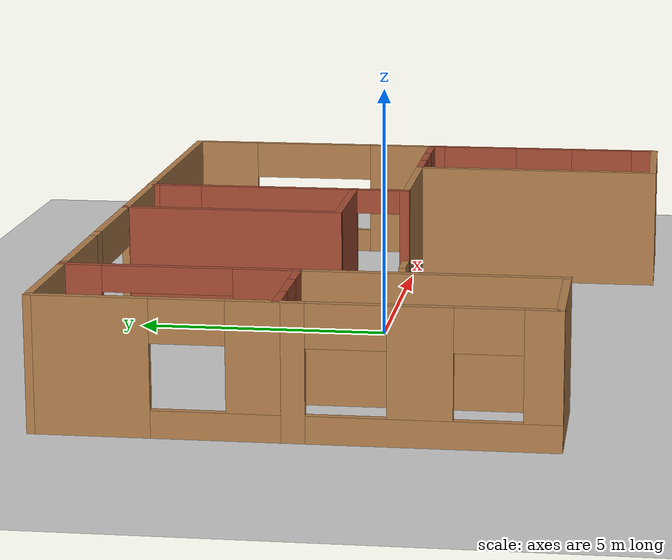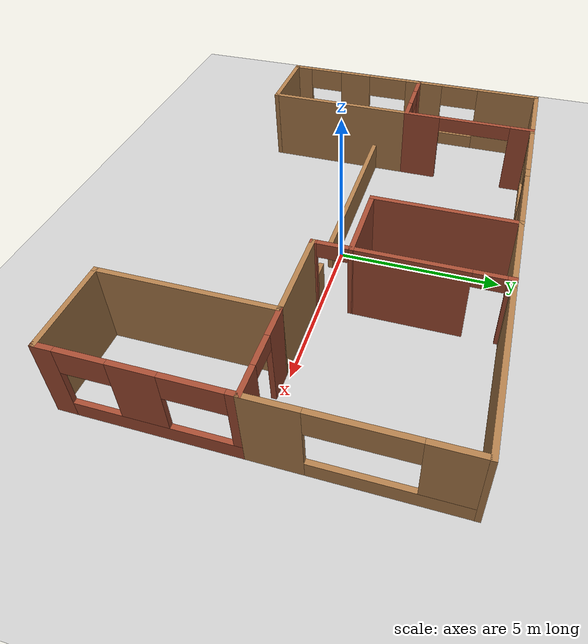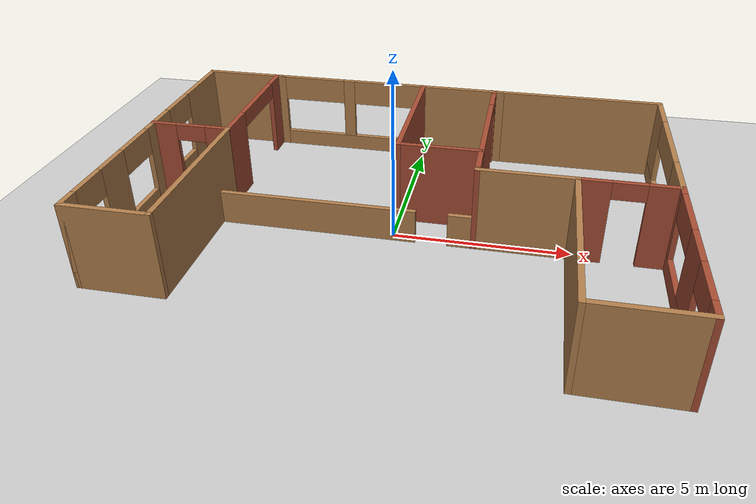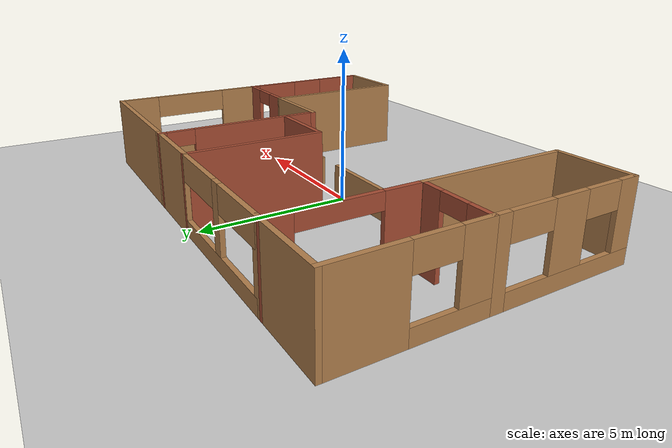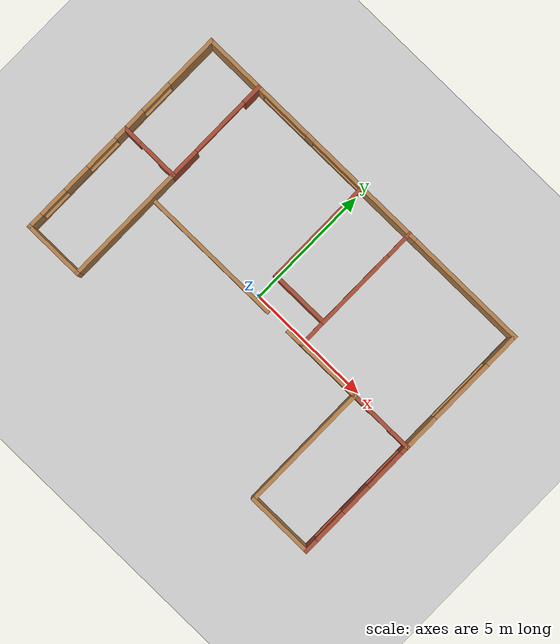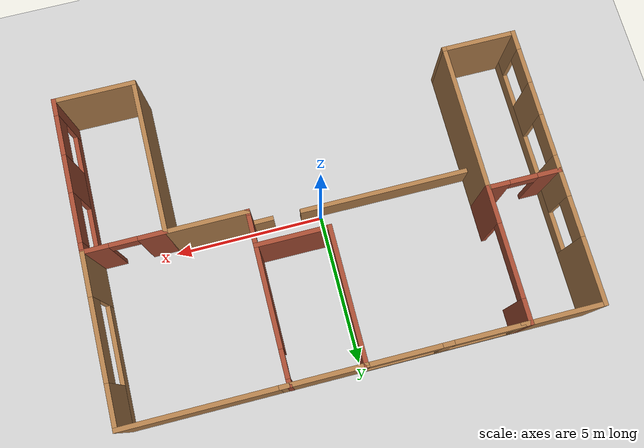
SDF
<sdf version="1.6">
 <world name="default">
  <light name="sun" type="directional">
   <pose>0 0 10 0 -0 0</pose>
   <diffuse>0.8 0.8 0.8 1</diffuse>
   <specular>0.2 0.2 0.2 1</specular>
   <attenuation>
    <range>1000</range>
    <constant>0.9</constant>
    <linear>0.01</linear>
    <quadratic>0.001</quadratic>
   </attenuation>
   <direction>-0.5 0.1 -0.9</direction>
  </light>
  <model name="ground_plane">
   <static>1</static>
   <link name="link">
    <collision name="collision">
     <geometry><plane><normal>0 0 1</normal><size>100 100</size></plane></geometry>
     <surface><friction><ode><mu>100</mu><mu2>50</mu2></ode></friction></surface>
    </collision>
    <visual name="visual">
     <cast_shadows>0</cast_shadows>
     <geometry><plane><normal>0 0 1</normal><size>100 100</size></plane></geometry>
     <material>
      <script><uri>file://media/materials/scripts/gazebo.material</uri><name>Gazebo/Grey</name></script>
     </material>
    </visual>
   </link>
  </model>
  <physics name="default_physics" default="0" type="ode">
   <real_time_update_rate>1000</real_time_update_rate>
   <max_step_size>0.001</max_step_size>
   <real_time_factor>1</real_time_factor>
   <ode>
    <solver>
     <type>quick</type>
     <iters>150</iters>
     <precon_iters>0</precon_iters>
     <sor>1.4</sor>
     <use_dynamic_moi_rescaling>1</use_dynamic_moi_rescaling>
    </solver>
    <constraints>
     <cfm>1e-05</cfm>
     <erp>0.2</erp>
     <contact_max_correcting_vel>2000</contact_max_correcting_vel>
     <contact_surface_layer>0.01</contact_surface_layer>
    </constraints>
   </ode>
  </physics>
  <model name="turtlebot3_house">
   <link name="Wall_101">
    <pose>-0.05 3.1 0 0 0 -1.5708</pose>
    <visual name="Wall_101_Visual">
     <pose>0 0 1.25 0 -0 0</pose>
     <geometry><box><size>4.5 0.15 2.5</size></box></geometry>
     <material>
      <script><uri>file://media/materials/scripts/gazebo.material</uri><name>Gazebo/Bricks</name></script>
      <ambient>1 1 1 1</ambient>
      <diffuse>1 1 1 1</diffuse>
      <specular>0.2 0.2 0.2 1</specular>
      <emissive>0 0 0 1</emissive>
     </material>
    </visual>
    <collision name="Wall_101_Collision">
     <pose>0 0 1.25 0 -0 0</pose>
     <geometry><box><size>4.5 0.15 2.5</size></box></geometry>
     <surface>
      <friction>
       <ode><mu>1</mu><mu2>1</mu2><fdir1>0 0 0</fdir1><slip1>0</slip1><slip2>0</slip2></ode>
       <torsional>
        <coefficient>1</coefficient>
        <patch_radius>0</patch_radius>
        <surface_radius>0</surface_radius>
        <use_patch_radius>1</use_patch_radius>
        <ode><slip>0</slip></ode>
       </torsional>
      </friction>
      <bounce><restitution_coefficient>0</restitution_coefficient><threshold>1e+06</threshold></bounce>
      <contact>
       <collide_without_contact>0</collide_without_contact>
       <collide_without_contact_bitmask>1</collide_without_contact_bitmask>
       <collide_bitmask>1</collide_bitmask>
       <ode>
        <soft_cfm>0</soft_cfm>
        <soft_erp>0.2</soft_erp>
        <kp>1e+13</kp>
        <kd>1</kd>
        <max_vel>0.01</max_vel>
        <min_depth>0</min_depth>
       </ode>
       <bullet>
        <split_impulse>1</split_impulse>
        <split_impulse_penetration_threshold>-0.01</split_impulse_penetration_threshold>
        <soft_cfm>0</soft_cfm>
        <soft_erp>0.2</soft_erp>
        <kp>1e+13</kp>
        <kd>1</kd>
       </bullet>
      </contact>
     </surface>
    </collision>
   </link>
   <link name="Wall_104">
    <pose>2.3 3.1 0 0 -0 1.5708</pose>
    <visual name="Wall_104_Visual_1">
     <pose>2.11625 0 1.25 0 -0 0</pose>
     <geometry><box><size>0.267504 0.15 2.5</size></box></geometry>
     <material>
      <script><uri>file://media/materials/scripts/gazebo.material</uri><name>Gazebo/Bricks</name></script>
      <ambient>1 1 1 1</ambient>
      <diffuse>1 1 1 1</diffuse>
      <specular>0.2 0.2 0.2 1</specular>
      <emissive>0 0 0 1</emissive>
     </material>
    </visual>
    <visual name="Wall_104_Visual_2">
     <pose>1.5325 0 2.25 0 -0 0</pose>
     <geometry><box><size>0.9 0.15 0.5</size></box></geometry>
     <material>
      <script><uri>file://media/materials/scripts/gazebo.material</uri><name>Gazebo/Bricks</name></script>
      <ambient>1 1 1 1</ambient>
      <diffuse>1 1 1 1</diffuse>
      <specular>0.2 0.2 0.2 1</specular>
      <emissive>0 0 0 1</emissive>
     </material>
    </visual>
    <visual name="Wall_104_Visual_0">
     <pose>-0.583752 0 1.25 0 -0 0</pose>
     <geometry><box><size>3.3325 0.15 2.5</size></box></geometry>
     <material>
      <script><uri>file://media/materials/scripts/gazebo.material</uri><name>Gazebo/Bricks</name></script>
      <ambient>1 1 1 1</ambient>
      <diffuse>1 1 1 1</diffuse>
      <specular>0.2 0.2 0.2 1</specular>
      <emissive>0 0 0 1</emissive>
     </material>
    </visual>
    <collision name="Wall_104_Collision_1">
     <pose>2.11625 0 1.25 0 -0 0</pose>
     <geometry><box><size>0.267504 0.15 2.5</size></box></geometry>
     <surface>
      <friction>
       <ode><mu>1</mu><mu2>1</mu2><fdir1>0 0 0</fdir1><slip1>0</slip1><slip2>0</slip2></ode>
       <torsional>
        <coefficient>1</coefficient>
        <patch_radius>0</patch_radius>
        <surface_radius>0</surface_radius>
        <use_patch_radius>1</use_patch_radius>
        <ode><slip>0</slip></ode>
       </torsional>
      </friction>
      <bounce><restitution_coefficient>0</restitution_coefficient><threshold>1e+06</threshold></bounce>
      <contact>
       <collide_without_contact>0</collide_without_contact>
       <collide_without_contact_bitmask>1</collide_without_contact_bitmask>
       <collide_bitmask>1</collide_bitmask>
       <ode>
        <soft_cfm>0</soft_cfm>
        <soft_erp>0.2</soft_erp>
        <kp>1e+13</kp>
        <kd>1</kd>
        <max_vel>0.01</max_vel>
        <min_depth>0</min_depth>
       </ode>
       <bullet>
        <split_impulse>1</split_impulse>
        <split_impulse_penetration_threshold>-0.01</split_impulse_penetration_threshold>
        <soft_cfm>0</soft_cfm>
        <soft_erp>0.2</soft_erp>
        <kp>1e+13</kp>
        <kd>1</kd>
       </bullet>
      </contact>
     </surface>
    </collision>
    <collision name="Wall_104_Collision_2">
     <pose>1.5325 0 2.25 0 -0 0</pose>
     <geometry><box><size>0.9 0.15 0.5</size></box></geometry>
     <surface>
      <friction>
       <ode><mu>1</mu><mu2>1</mu2><fdir1>0 0 0</fdir1><slip1>0</slip1><slip2>0</slip2></ode>
       <torsional>
        <coefficient>1</coefficient>
        <patch_radius>0</patch_radius>
        <surface_radius>0</surface_radius>
        <use_patch_radius>1</use_patch_radius>
        <ode><slip>0</slip></ode>
       </torsional>
      </friction>
      <bounce><restitution_coefficient>0</restitution_coefficient><threshold>1e+06</threshold></bounce>
      <contact>
       <collide_without_contact>0</collide_without_contact>
       <collide_without_contact_bitmask>1</collide_without_contact_bitmask>
       <collide_bitmask>1</collide_bitmask>
       <ode>
        <soft_cfm>0</soft_cfm>
        <soft_erp>0.2</soft_erp>
        <kp>1e+13</kp>
        <kd>1</kd>
        <max_vel>0.01</max_vel>
        <min_depth>0</min_depth>
       </ode>
       <bullet>
        <split_impulse>1</split_impulse>
        <split_impulse_penetration_threshold>-0.01</split_impulse_penetration_threshold>
        <soft_cfm>0</soft_cfm>
        <soft_erp>0.2</soft_erp>
        <kp>1e+13</kp>
        <kd>1</kd>
       </bullet>
      </contact>
     </surface>
    </collision>
    <collision name="Wall_104_Collision_0">
     <pose>-0.583752 0 1.25 0 -0 0</pose>
     <geometry><box><size>3.3325 0.15 2.5</size></box></geometry>
     <surface>
      <friction>
       <ode><mu>1</mu><mu2>1</mu2><fdir1>0 0 0</fdir1><slip1>0</slip1><slip2>0</slip2></ode>
       <torsional>
        <coefficient>1</coefficient>
        <patch_radius>0</patch_radius>
        <surface_radius>0</surface_radius>
        <use_patch_radius>1</use_patch_radius>
        <ode><slip>0</slip></ode>
       </torsional>
      </friction>
      <bounce><restitution_coefficient>0</restitution_coefficient><threshold>1e+06</threshold></bounce>
      <contact>
       <collide_without_contact>0</collide_without_contact>
       <collide_without_contact_bitmask>1</collide_without_contact_bitmask>
       <collide_bitmask>1</collide_bitmask>
       <ode>
        <soft_cfm>0</soft_cfm>
        <soft_erp>0.2</soft_erp>
        <kp>1e+13</kp>
        <kd>1</kd>
        <max_vel>0.01</max_vel>
        <min_depth>0</min_depth>
       </ode>
       <bullet>
        <split_impulse>1</split_impulse>
        <split_impulse_penetration_threshold>-0.01</split_impulse_penetration_threshold>
        <soft_cfm>0</soft_cfm>
        <soft_erp>0.2</soft_erp>
        <kp>1e+13</kp>
        <kd>1</kd>
       </bullet>
      </contact>
     </surface>
    </collision>
   </link>
   <link name="Wall_106">
    <pose>6.2 -0.175 0 0 -0 0</pose>
    <visual name="Wall_106_Visual_1">
     <pose>0.922235 0 1.25 0 -0 0</pose>
     <geometry><box><size>0.905529 0.15 2.5</size></box></geometry>
     <material>
      <script><uri>file://media/materials/scripts/gazebo.material</uri><name>Gazebo/Bricks</name></script>
      <ambient>1 1 1 1</ambient>
      <diffuse>1 1 1 1</diffuse>
      <specular>0.2 0.2 0.2 1</specular>
      <emissive>0 0 0 1</emissive>
     </material>
    </visual>
    <visual name="Wall_106_Visual_2">
     <pose>0.019471 0 2.25 0 -0 0</pose>
     <geometry><box><size>0.9 0.15 0.5</size></box></geometry>
     <material>
      <script><uri>file://media/materials/scripts/gazebo.material</uri><name>Gazebo/Bricks</name></script>
      <ambient>1 1 1 1</ambient>
      <diffuse>1 1 1 1</diffuse>
      <specular>0.2 0.2 0.2 1</specular>
      <emissive>0 0 0 1</emissive>
     </material>
    </visual>
    <visual name="Wall_106_Visual_0">
     <pose>-0.902765 0 1.25 0 -0 0</pose>
     <geometry><box><size>0.944471 0.15 2.5</size></box></geometry>
     <material>
      <script><uri>file://media/materials/scripts/gazebo.material</uri><name>Gazebo/Bricks</name></script>
      <ambient>1 1 1 1</ambient>
      <diffuse>1 1 1 1</diffuse>
      <specular>0.2 0.2 0.2 1</specular>
      <emissive>0 0 0 1</emissive>
     </material>
    </visual>
    <collision name="Wall_106_Collision_1">
     <pose>0.922235 0 1.25 0 -0 0</pose>
     <geometry><box><size>0.905529 0.15 2.5</size></box></geometry>
     <surface>
      <friction>
       <ode><mu>1</mu><mu2>1</mu2><fdir1>0 0 0</fdir1><slip1>0</slip1><slip2>0</slip2></ode>
       <torsional>
        <coefficient>1</coefficient>
        <patch_radius>0</patch_radius>
        <surface_radius>0</surface_radius>
        <use_patch_radius>1</use_patch_radius>
        <ode><slip>0</slip></ode>
       </torsional>
      </friction>
      <bounce><restitution_coefficient>0</restitution_coefficient><threshold>1e+06</threshold></bounce>
      <contact>
       <collide_without_contact>0</collide_without_contact>
       <collide_without_contact_bitmask>1</collide_without_contact_bitmask>
       <collide_bitmask>1</collide_bitmask>
       <ode>
        <soft_cfm>0</soft_cfm>
        <soft_erp>0.2</soft_erp>
        <kp>1e+13</kp>
        <kd>1</kd>
        <max_vel>0.01</max_vel>
        <min_depth>0</min_depth>
       </ode>
       <bullet>
        <split_impulse>1</split_impulse>
        <split_impulse_penetration_threshold>-0.01</split_impulse_penetration_threshold>
        <soft_cfm>0</soft_cfm>
        <soft_erp>0.2</soft_erp>
        <kp>1e+13</kp>
        <kd>1</kd>
       </bullet>
      </contact>
     </surface>
    </collision>
    <collision name="Wall_106_Collision_0">
     <pose>-0.902765 0 1.25 0 -0 0</pose>
     <geometry><box><size>0.944471 0.15 2.5</size></box></geometry>
     <surface>
      <friction>
       <ode><mu>1</mu><mu2>1</mu2><fdir1>0 0 0</fdir1><slip1>0</slip1><slip2>0</slip2></ode>
       <torsional>
        <coefficient>1</coefficient>
        <patch_radius>0</patch_radius>
        <surface_radius>0</surface_radius>
        <use_patch_radius>1</use_patch_radius>
        <ode><slip>0</slip></ode>
       </torsional>
      </friction>
      <bounce><restitution_coefficient>0</restitution_coefficient><threshold>1e+06</threshold></bounce>
      <contact>
       <collide_without_contact>0</collide_without_contact>
       <collide_without_contact_bitmask>1</collide_without_contact_bitmask>
       <collide_bitmask>1</collide_bitmask>
       <ode>
        <soft_cfm>0</soft_cfm>
        <soft_erp>0.2</soft_erp>
        <kp>1e+13</kp>
        <kd>1</kd>
        <max_vel>0.01</max_vel>
        <min_depth>0</min_depth>
       </ode>
       <bullet>
        <split_impulse>1</split_impulse>
        <split_impulse_penetration_threshold>-0.01</split_impulse_penetration_threshold>
        <soft_cfm>0</soft_cfm>
        <soft_erp>0.2</soft_erp>
        <kp>1e+13</kp>
        <kd>1</kd>
       </bullet>
      </contact>
     </surface>
    </collision>
    <collision name="Wall_106_Collision_2">
     <pose>0.019471 0 2.25 0 -0 0</pose>
     <geometry><box><size>0.9 0.15 0.5</size></box></geometry>
     <surface>
      <friction>
       <ode><mu>1</mu><mu2>1</mu2><fdir1>0 0 0</fdir1><slip1>0</slip1><slip2>0</slip2></ode>
       <torsional>
        <coefficient>1</coefficient>
        <patch_radius>0</patch_radius>
        <surface_radius>0</surface_radius>
        <use_patch_radius>1</use_patch_radius>
        <ode><slip>0</slip></ode>
       </torsional>
      </friction>
      <bounce><restitution_coefficient>0</restitution_coefficient><threshold>1e+06</threshold></bounce>
      <contact>
       <collide_without_contact>0</collide_without_contact>
       <collide_without_contact_bitmask>1</collide_without_contact_bitmask>
       <collide_bitmask>1</collide_bitmask>
       <ode>
        <soft_cfm>0</soft_cfm>
        <soft_erp>0.2</soft_erp>
        <kp>1e+13</kp>
        <kd>1</kd>
        <max_vel>0.01</max_vel>
        <min_depth>0</min_depth>
       </ode>
       <bullet>
        <split_impulse>1</split_impulse>
        <split_impulse_penetration_threshold>-0.01</split_impulse_penetration_threshold>
        <soft_cfm>0</soft_cfm>
        <soft_erp>0.2</soft_erp>
        <kp>1e+13</kp>
        <kd>1</kd>
       </bullet>
      </contact>
     </surface>
    </collision>
   </link>
   <link name="Wall_108">
    <pose>-1.37512 -0.17488 0 0 -0 0</pose>
    <visual name="Wall_108_Visual_0">
     <pose>-0.856324 0 0.5 0 -0 0</pose>
     <geometry><box><size>5.78735 0.15 1</size></box></geometry>
     <material>
      <script><uri>file://media/materials/scripts/gazebo.material</uri><name>Gazebo/Wood</name></script>
      <ambient>1 1 1 1</ambient>
      <diffuse>1 1 1 1</diffuse>
      <specular>0.2 0.2 0.2 1</specular>
      <emissive>0 0 0 1</emissive>
     </material>
    </visual>
    <visual name="Wall_108_Visual_1">
     <pose>3.34368 0 0.5 0 -0 0</pose>
     <geometry><box><size>0.812647 0.15 1</size></box></geometry>
     <material>
      <script><uri>file://media/materials/scripts/gazebo.material</uri><name>Gazebo/Wood</name></script>
      <ambient>1 1 1 1</ambient>
      <diffuse>1 1 1 1</diffuse>
      <specular>0.2 0.2 0.2 1</specular>
      <emissive>0 0 0 1</emissive>
     </material>
    </visual>
    <collision name="Wall_108_Collision_1">
     <pose>3.34368 0 0.5 0 -0 0</pose>
     <geometry><box><size>0.812647 0.15 1</size></box></geometry>
     <surface>
      <friction>
       <ode><mu>1</mu><mu2>1</mu2><fdir1>0 0 0</fdir1><slip1>0</slip1><slip2>0</slip2></ode>
       <torsional>
        <coefficient>1</coefficient>
        <patch_radius>0</patch_radius>
        <surface_radius>0</surface_radius>
        <use_patch_radius>1</use_patch_radius>
        <ode><slip>0</slip></ode>
       </torsional>
      </friction>
      <bounce><restitution_coefficient>0</restitution_coefficient><threshold>1e+06</threshold></bounce>
      <contact>
       <collide_without_contact>0</collide_without_contact>
       <collide_without_contact_bitmask>1</collide_without_contact_bitmask>
       <collide_bitmask>1</collide_bitmask>
       <ode>
        <soft_cfm>0</soft_cfm>
        <soft_erp>0.2</soft_erp>
        <kp>1e+13</kp>
        <kd>1</kd>
        <max_vel>0.01</max_vel>
        <min_depth>0</min_depth>
       </ode>
       <bullet>
        <split_impulse>1</split_impulse>
        <split_impulse_penetration_threshold>-0.01</split_impulse_penetration_threshold>
        <soft_cfm>0</soft_cfm>
        <soft_erp>0.2</soft_erp>
        <kp>1e+13</kp>
        <kd>1</kd>
       </bullet>
      </contact>
     </surface>
    </collision>
    <collision name="Wall_108_Collision_0">
     <pose>-0.856324 0 0.5 0 -0 0</pose>
     <geometry><box><size>5.78735 0.15 1</size></box></geometry>
     <surface>
      <friction>
       <ode><mu>1</mu><mu2>1</mu2><fdir1>0 0 0</fdir1><slip1>0</slip1><slip2>0</slip2></ode>
       <torsional>
        <coefficient>1</coefficient>
        <patch_radius>0</patch_radius>
        <surface_radius>0</surface_radius>
        <use_patch_radius>1</use_patch_radius>
        <ode><slip>0</slip></ode>
       </torsional>
      </friction>
      <bounce><restitution_coefficient>0</restitution_coefficient><threshold>1e+06</threshold></bounce>
      <contact>
       <collide_without_contact>0</collide_without_contact>
       <collide_without_contact_bitmask>1</collide_without_contact_bitmask>
       <collide_bitmask>1</collide_bitmask>
       <ode>
        <soft_cfm>0</soft_cfm>
        <soft_erp>0.2</soft_erp>
        <kp>1e+13</kp>
        <kd>1</kd>
        <max_vel>0.01</max_vel>
        <min_depth>0</min_depth>
       </ode>
       <bullet>
        <split_impulse>1</split_impulse>
        <split_impulse_penetration_threshold>-0.01</split_impulse_penetration_threshold>
        <soft_cfm>0</soft_cfm>
        <soft_erp>0.2</soft_erp>
        <kp>1e+13</kp>
        <kd>1</kd>
       </bullet>
      </contact>
     </surface>
    </collision>
   </link>
   <link name="Wall_81">
    <pose>5.07752 5.2688 0 0 -0 3.14159</pose>
    <visual name="Wall_81_Visual">
     <pose>0 0 1.25 0 -0 0</pose>
     <geometry><box><size>5 0.15 2.5</size></box></geometry>
     <material>
      <script><uri>file://media/materials/scripts/gazebo.material</uri><name>Gazebo/Wood</name></script>
      <ambient>1 1 1 1</ambient>
      <diffuse>1 1 1 1</diffuse>
      <specular>0.2 0.2 0.2 1</specular>
      <emissive>0 0 0 1</emissive>
     </material>
    </visual>
    <collision name="Wall_81_Collision">
     <pose>0 0 1.25 0 -0 0</pose>
     <geometry><box><size>5 0.15 2.5</size></box></geometry>
     <surface>
      <friction>
       <ode><mu>1</mu><mu2>1</mu2><fdir1>0 0 0</fdir1><slip1>0</slip1><slip2>0</slip2></ode>
       <torsional>
        <coefficient>1</coefficient>
        <patch_radius>0</patch_radius>
        <surface_radius>0</surface_radius>
        <use_patch_radius>1</use_patch_radius>
        <ode><slip>0</slip></ode>
       </torsional>
      </friction>
      <bounce><restitution_coefficient>0</restitution_coefficient><threshold>1e+06</threshold></bounce>
      <contact>
       <collide_without_contact>0</collide_without_contact>
       <collide_without_contact_bitmask>1</collide_without_contact_bitmask>
       <collide_bitmask>1</collide_bitmask>
       <ode>
        <soft_cfm>0</soft_cfm>
        <soft_erp>0.2</soft_erp>
        <kp>1e+13</kp>
        <kd>1</kd>
        <max_vel>0.01</max_vel>
        <min_depth>0</min_depth>
       </ode>
       <bullet>
        <split_impulse>1</split_impulse>
        <split_impulse_penetration_threshold>-0.01</split_impulse_penetration_threshold>
        <soft_cfm>0</soft_cfm>
        <soft_erp>0.2</soft_erp>
        <kp>1e+13</kp>
        <kd>1</kd>
       </bullet>
      </contact>
     </surface>
    </collision>
   </link>
   <link name="Wall_82">
    <pose>1.25 5.26876 0 0 -0 3.14159</pose>
    <visual name="Wall_82_Visual">
     <pose>0 0 1.25 0 -0 0</pose>
     <geometry><box><size>2.75 0.15 2.5</size></box></geometry>
     <material>
      <script><uri>file://media/materials/scripts/gazebo.material</uri><name>Gazebo/Wood</name></script>
      <ambient>1 1 1 1</ambient>
      <diffuse>1 1 1 1</diffuse>
      <specular>0.2 0.2 0.2 1</specular>
      <emissive>0 0 0 1</emissive>
     </material>
    </visual>
    <collision name="Wall_82_Collision">
     <pose>0 0 1.25 0 -0 0</pose>
     <geometry><box><size>2.75 0.15 2.5</size></box></geometry>
     <surface>
      <friction>
       <ode><mu>1</mu><mu2>1</mu2><fdir1>0 0 0</fdir1><slip1>0</slip1><slip2>0</slip2></ode>
       <torsional>
        <coefficient>1</coefficient>
        <patch_radius>0</patch_radius>
        <surface_radius>0</surface_radius>
        <use_patch_radius>1</use_patch_radius>
        <ode><slip>0</slip></ode>
       </torsional>
      </friction>
      <bounce><restitution_coefficient>0</restitution_coefficient><threshold>1e+06</threshold></bounce>
      <contact>
       <collide_without_contact>0</collide_without_contact>
       <collide_without_contact_bitmask>1</collide_without_contact_bitmask>
       <collide_bitmask>1</collide_bitmask>
       <ode>
        <soft_cfm>0</soft_cfm>
        <soft_erp>0.2</soft_erp>
        <kp>1e+13</kp>
        <kd>1</kd>
        <max_vel>0.01</max_vel>
        <min_depth>0</min_depth>
       </ode>
       <bullet>
        <split_impulse>1</split_impulse>
        <split_impulse_penetration_threshold>-0.01</split_impulse_penetration_threshold>
        <soft_cfm>0</soft_cfm>
        <soft_erp>0.2</soft_erp>
        <kp>1e+13</kp>
        <kd>1</kd>
       </bullet>
      </contact>
     </surface>
    </collision>
   </link>
   <link name="Wall_83">
    <pose>-2.475 5.275 0 0 -0 3.14159</pose>
    <visual name="Wall_83_Visual_2">
     <pose>0.110246 0 1.5 0 -0 0</pose>
     <geometry><box><size>0.37052 0.15 2</size></box></geometry>
     <material>
      <script><uri>file://media/materials/scripts/gazebo.material</uri><name>Gazebo/Wood</name></script>
      <ambient>1 1 1 1</ambient>
      <diffuse>1 1 1 1</diffuse>
      <specular>0.2 0.2 0.2 1</specular>
      <emissive>0 0 0 1</emissive>
     </material>
    </visual>
    <visual name="Wall_83_Visual_6">
     <pose>1.39775 0 2.1 0 -0 0</pose>
     <geometry><box><size>2.20449 0.15 0.8</size></box></geometry>
     <material>
      <script><uri>file://media/materials/scripts/gazebo.material</uri><name>Gazebo/Wood</name></script>
      <ambient>1 1 1 1</ambient>
      <diffuse>1 1 1 1</diffuse>
      <specular>0.2 0.2 0.2 1</specular>
      <emissive>0 0 0 1</emissive>
     </material>
    </visual>
    <visual name="Wall_83_Visual_3">
     <pose>0.110246 0 1.5 0 -0 0</pose>
     <geometry><box><size>0.37052 0.15 2</size></box></geometry>
     <material>
      <script><uri>file://media/materials/scripts/gazebo.material</uri><name>Gazebo/Wood</name></script>
      <ambient>1 1 1 1</ambient>
      <diffuse>1 1 1 1</diffuse>
      <specular>0.2 0.2 0.2 1</specular>
      <emissive>0 0 0 1</emissive>
     </material>
    </visual>
    <visual name="Wall_83_Visual_1">
     <pose>0.080993 0 0.25 0 -0 0</pose>
     <geometry><box><size>4.83801 0.15 0.5</size></box></geometry>
     <material>
      <script><uri>file://media/materials/scripts/gazebo.material</uri><name>Gazebo/Wood</name></script>
      <ambient>1 1 1 1</ambient>
      <diffuse>1 1 1 1</diffuse>
      <specular>0.2 0.2 0.2 1</specular>
      <emissive>0 0 0 1</emissive>
     </material>
    </visual>
    <visual name="Wall_83_Visual_4">
     <pose>-1.20651 0 2.1 0 -0 0</pose>
     <geometry><box><size>2.263 0.15 0.8</size></box></geometry>
     <material>
      <script><uri>file://media/materials/scripts/gazebo.material</uri><name>Gazebo/Wood</name></script>
      <ambient>1 1 1 1</ambient>
      <diffuse>1 1 1 1</diffuse>
      <specular>0.2 0.2 0.2 1</specular>
      <emissive>0 0 0 1</emissive>
     </material>
    </visual>
    <visual name="Wall_83_Visual_5">
     <pose>1.39775 0 2.1 0 -0 0</pose>
     <geometry><box><size>2.20449 0.15 0.8</size></box></geometry>
     <material>
      <script><uri>file://media/materials/scripts/gazebo.material</uri><name>Gazebo/Wood</name></script>
      <ambient>1 1 1 1</ambient>
      <diffuse>1 1 1 1</diffuse>
      <specular>0.2 0.2 0.2 1</specular>
      <emissive>0 0 0 1</emissive>
     </material>
    </visual>
    <visual name="Wall_83_Visual_0">
     <pose>-2.41901 0 1.25 0 -0 0</pose>
     <geometry><box><size>0.161986 0.15 2.5</size></box></geometry>
     <material>
      <script><uri>file://media/materials/scripts/gazebo.material</uri><name>Gazebo/Wood</name></script>
      <ambient>1 1 1 1</ambient>
      <diffuse>1 1 1 1</diffuse>
      <specular>0.2 0.2 0.2 1</specular>
      <emissive>0 0 0 1</emissive>
     </material>
    </visual>
    <collision name="Wall_83_Collision_4">
     <pose>-1.20651 0 2.1 0 -0 0</pose>
     <geometry><box><size>2.263 0.15 0.8</size></box></geometry>
     <surface>
      <friction>
       <ode><mu>1</mu><mu2>1</mu2><fdir1>0 0 0</fdir1><slip1>0</slip1><slip2>0</slip2></ode>
       <torsional>
        <coefficient>1</coefficient>
        <patch_radius>0</patch_radius>
        <surface_radius>0</surface_radius>
        <use_patch_radius>1</use_patch_radius>
        <ode><slip>0</slip></ode>
       </torsional>
      </friction>
      <bounce><restitution_coefficient>0</restitution_coefficient><threshold>1e+06</threshold></bounce>
      <contact>
       <collide_without_contact>0</collide_without_contact>
       <collide_without_contact_bitmask>1</collide_without_contact_bitmask>
       <collide_bitmask>1</collide_bitmask>
       <ode>
        <soft_cfm>0</soft_cfm>
        <soft_erp>0.2</soft_erp>
        <kp>1e+13</kp>
        <kd>1</kd>
        <max_vel>0.01</max_vel>
        <min_depth>0</min_depth>
       </ode>
       <bullet>
        <split_impulse>1</split_impulse>
        <split_impulse_penetration_threshold>-0.01</split_impulse_penetration_threshold>
        <soft_cfm>0</soft_cfm>
        <soft_erp>0.2</soft_erp>
        <kp>1e+13</kp>
        <kd>1</kd>
       </bullet>
      </contact>
     </surface>
    </collision>
    <collision name="Wall_83_Collision_2">
     <pose>0.110246 0 1.5 0 -0 0</pose>
     <geometry><box><size>0.37052 0.15 2</size></box></geometry>
     <surface>
      <friction>
       <ode><mu>1</mu><mu2>1</mu2><fdir1>0 0 0</fdir1><slip1>0</slip1><slip2>0</slip2></ode>
       <torsional>
        <coefficient>1</coefficient>
        <patch_radius>0</patch_radius>
        <surface_radius>0</surface_radius>
        <use_patch_radius>1</use_patch_radius>
        <ode><slip>0</slip></ode>
       </torsional>
      </friction>
      <bounce><restitution_coefficient>0</restitution_coefficient><threshold>1e+06</threshold></bounce>
      <contact>
       <collide_without_contact>0</collide_without_contact>
       <collide_without_contact_bitmask>1</collide_without_contact_bitmask>
       <collide_bitmask>1</collide_bitmask>
       <ode>
        <soft_cfm>0</soft_cfm>
        <soft_erp>0.2</soft_erp>
        <kp>1e+13</kp>
        <kd>1</kd>
        <max_vel>0.01</max_vel>
        <min_depth>0</min_depth>
       </ode>
       <bullet>
        <split_impulse>1</split_impulse>
        <split_impulse_penetration_threshold>-0.01</split_impulse_penetration_threshold>
        <soft_cfm>0</soft_cfm>
        <soft_erp>0.2</soft_erp>
        <kp>1e+13</kp>
        <kd>1</kd>
       </bullet>
      </contact>
     </surface>
    </collision>
    <collision name="Wall_83_Collision_6">
     <pose>1.39775 0 2.1 0 -0 0</pose>
     <geometry><box><size>2.20449 0.15 0.8</size></box></geometry>
     <surface>
      <friction>
       <ode><mu>1</mu><mu2>1</mu2><fdir1>0 0 0</fdir1><slip1>0</slip1><slip2>0</slip2></ode>
       <torsional>
        <coefficient>1</coefficient>
        <patch_radius>0</patch_radius>
        <surface_radius>0</surface_radius>
        <use_patch_radius>1</use_patch_radius>
        <ode><slip>0</slip></ode>
       </torsional>
      </friction>
      <bounce><restitution_coefficient>0</restitution_coefficient><threshold>1e+06</threshold></bounce>
      <contact>
       <collide_without_contact>0</collide_without_contact>
       <collide_without_contact_bitmask>1</collide_without_contact_bitmask>
       <collide_bitmask>1</collide_bitmask>
       <ode>
        <soft_cfm>0</soft_cfm>
        <soft_erp>0.2</soft_erp>
        <kp>1e+13</kp>
        <kd>1</kd>
        <max_vel>0.01</max_vel>
        <min_depth>0</min_depth>
       </ode>
       <bullet>
        <split_impulse>1</split_impulse>
        <split_impulse_penetration_threshold>-0.01</split_impulse_penetration_threshold>
        <soft_cfm>0</soft_cfm>
        <soft_erp>0.2</soft_erp>
        <kp>1e+13</kp>
        <kd>1</kd>
       </bullet>
      </contact>
     </surface>
    </collision>
    <collision name="Wall_83_Collision_0">
     <pose>-2.41901 0 1.25 0 -0 0</pose>
     <geometry><box><size>0.161986 0.15 2.5</size></box></geometry>
     <surface>
      <friction>
       <ode><mu>1</mu><mu2>1</mu2><fdir1>0 0 0</fdir1><slip1>0</slip1><slip2>0</slip2></ode>
       <torsional>
        <coefficient>1</coefficient>
        <patch_radius>0</patch_radius>
        <surface_radius>0</surface_radius>
        <use_patch_radius>1</use_patch_radius>
        <ode><slip>0</slip></ode>
       </torsional>
      </friction>
      <bounce><restitution_coefficient>0</restitution_coefficient><threshold>1e+06</threshold></bounce>
      <contact>
       <collide_without_contact>0</collide_without_contact>
       <collide_without_contact_bitmask>1</collide_without_contact_bitmask>
       <collide_bitmask>1</collide_bitmask>
       <ode>
        <soft_cfm>0</soft_cfm>
        <soft_erp>0.2</soft_erp>
        <kp>1e+13</kp>
        <kd>1</kd>
        <max_vel>0.01</max_vel>
        <min_depth>0</min_depth>
       </ode>
       <bullet>
        <split_impulse>1</split_impulse>
        <split_impulse_penetration_threshold>-0.01</split_impulse_penetration_threshold>
        <soft_cfm>0</soft_cfm>
        <soft_erp>0.2</soft_erp>
        <kp>1e+13</kp>
        <kd>1</kd>
       </bullet>
      </contact>
     </surface>
    </collision>
    <collision name="Wall_83_Collision_1">
     <pose>0.080993 0 0.25 0 -0 0</pose>
     <geometry><box><size>4.83801 0.15 0.5</size></box></geometry>
     <surface>
      <friction>
       <ode><mu>1</mu><mu2>1</mu2><fdir1>0 0 0</fdir1><slip1>0</slip1><slip2>0</slip2></ode>
       <torsional>
        <coefficient>1</coefficient>
        <patch_radius>0</patch_radius>
        <surface_radius>0</surface_radius>
        <use_patch_radius>1</use_patch_radius>
        <ode><slip>0</slip></ode>
       </torsional>
      </friction>
      <bounce><restitution_coefficient>0</restitution_coefficient><threshold>1e+06</threshold></bounce>
      <contact>
       <collide_without_contact>0</collide_without_contact>
       <collide_without_contact_bitmask>1</collide_without_contact_bitmask>
       <collide_bitmask>1</collide_bitmask>
       <ode>
        <soft_cfm>0</soft_cfm>
        <soft_erp>0.2</soft_erp>
        <kp>1e+13</kp>
        <kd>1</kd>
        <max_vel>0.01</max_vel>
        <min_depth>0</min_depth>
       </ode>
       <bullet>
        <split_impulse>1</split_impulse>
        <split_impulse_penetration_threshold>-0.01</split_impulse_penetration_threshold>
        <soft_cfm>0</soft_cfm>
        <soft_erp>0.2</soft_erp>
        <kp>1e+13</kp>
        <kd>1</kd>
       </bullet>
      </contact>
     </surface>
    </collision>
    <collision name="Wall_83_Collision_3">
     <pose>0.110246 0 1.5 0 -0 0</pose>
     <geometry><box><size>0.37052 0.15 2</size></box></geometry>
     <surface>
      <friction>
       <ode><mu>1</mu><mu2>1</mu2><fdir1>0 0 0</fdir1><slip1>0</slip1><slip2>0</slip2></ode>
       <torsional>
        <coefficient>1</coefficient>
        <patch_radius>0</patch_radius>
        <surface_radius>0</surface_radius>
        <use_patch_radius>1</use_patch_radius>
        <ode><slip>0</slip></ode>
       </torsional>
      </friction>
      <bounce><restitution_coefficient>0</restitution_coefficient><threshold>1e+06</threshold></bounce>
      <contact>
       <collide_without_contact>0</collide_without_contact>
       <collide_without_contact_bitmask>1</collide_without_contact_bitmask>
       <collide_bitmask>1</collide_bitmask>
       <ode>
        <soft_cfm>0</soft_cfm>
        <soft_erp>0.2</soft_erp>
        <kp>1e+13</kp>
        <kd>1</kd>
        <max_vel>0.01</max_vel>
        <min_depth>0</min_depth>
       </ode>
       <bullet>
        <split_impulse>1</split_impulse>
        <split_impulse_penetration_threshold>-0.01</split_impulse_penetration_threshold>
        <soft_cfm>0</soft_cfm>
        <soft_erp>0.2</soft_erp>
        <kp>1e+13</kp>
        <kd>1</kd>
       </bullet>
      </contact>
     </surface>
    </collision>
    <collision name="Wall_83_Collision_5">
     <pose>1.39775 0 2.1 0 -0 0</pose>
     <geometry><box><size>2.20449 0.15 0.8</size></box></geometry>
     <surface>
      <friction>
       <ode><mu>1</mu><mu2>1</mu2><fdir1>0 0 0</fdir1><slip1>0</slip1><slip2>0</slip2></ode>
       <torsional>
        <coefficient>1</coefficient>
        <patch_radius>0</patch_radius>
        <surface_radius>0</surface_radius>
        <use_patch_radius>1</use_patch_radius>
        <ode><slip>0</slip></ode>
       </torsional>
      </friction>
      <bounce><restitution_coefficient>0</restitution_coefficient><threshold>1e+06</threshold></bounce>
      <contact>
       <collide_without_contact>0</collide_without_contact>
       <collide_without_contact_bitmask>1</collide_without_contact_bitmask>
       <collide_bitmask>1</collide_bitmask>
       <ode>
        <soft_cfm>0</soft_cfm>
        <soft_erp>0.2</soft_erp>
        <kp>1e+13</kp>
        <kd>1</kd>
        <max_vel>0.01</max_vel>
        <min_depth>0</min_depth>
       </ode>
       <bullet>
        <split_impulse>1</split_impulse>
        <split_impulse_penetration_threshold>-0.01</split_impulse_penetration_threshold>
        <soft_cfm>0</soft_cfm>
        <soft_erp>0.2</soft_erp>
        <kp>1e+13</kp>
        <kd>1</kd>
       </bullet>
      </contact>
     </surface>
    </collision>
   </link>
   <link name="Wall_84">
    <pose>-6.2 5.275 0 0 -0 3.14159</pose>
    <visual name="Wall_84_Visual">
     <pose>0 0 1.25 0 -0 0</pose>
     <geometry><box><size>2.75 0.15 2.5</size></box></geometry>
     <material>
      <script><uri>file://media/materials/scripts/gazebo.material</uri><name>Gazebo/Wood</name></script>
      <ambient>1 1 1 1</ambient>
      <diffuse>1 1 1 1</diffuse>
      <specular>0.2 0.2 0.2 1</specular>
      <emissive>0 0 0 1</emissive>
     </material>
    </visual>
    <collision name="Wall_84_Collision">
     <pose>0 0 1.25 0 -0 0</pose>
     <geometry><box><size>2.75 0.15 2.5</size></box></geometry>
     <surface>
      <friction>
       <ode><mu>1</mu><mu2>1</mu2><fdir1>0 0 0</fdir1><slip1>0</slip1><slip2>0</slip2></ode>
       <torsional>
        <coefficient>1</coefficient>
        <patch_radius>0</patch_radius>
        <surface_radius>0</surface_radius>
        <use_patch_radius>1</use_patch_radius>
        <ode><slip>0</slip></ode>
       </torsional>
      </friction>
      <bounce><restitution_coefficient>0</restitution_coefficient><threshold>1e+06</threshold></bounce>
      <contact>
       <collide_without_contact>0</collide_without_contact>
       <collide_without_contact_bitmask>1</collide_without_contact_bitmask>
       <collide_bitmask>1</collide_bitmask>
       <ode>
        <soft_cfm>0</soft_cfm>
        <soft_erp>0.2</soft_erp>
        <kp>1e+13</kp>
        <kd>1</kd>
        <max_vel>0.01</max_vel>
        <min_depth>0</min_depth>
       </ode>
       <bullet>
        <split_impulse>1</split_impulse>
        <split_impulse_penetration_threshold>-0.01</split_impulse_penetration_threshold>
        <soft_cfm>0</soft_cfm>
        <soft_erp>0.2</soft_erp>
        <kp>1e+13</kp>
        <kd>1</kd>
       </bullet>
      </contact>
     </surface>
    </collision>
   </link>
   <link name="Wall_85">
    <pose>-7.5 3.1 0 0 0 -1.5708</pose>
    <visual name="Wall_85_Visual_3">
     <pose>0.62212 0 2.1 0 -0 0</pose>
     <geometry><box><size>1.332 0.15 0.8</size></box></geometry>
     <material>
      <script><uri>file://media/materials/scripts/gazebo.material</uri><name>Gazebo/Wood</name></script>
      <ambient>1 1 1 1</ambient>
      <diffuse>1 1 1 1</diffuse>
      <specular>0.2 0.2 0.2 1</specular>
      <emissive>0 0 0 1</emissive>
     </material>
    </visual>
    <visual name="Wall_85_Visual_2">
     <pose>1.76906 0 1.5 0 -0 0</pose>
     <geometry><box><size>0.96188 0.15 2</size></box></geometry>
     <material>
      <script><uri>file://media/materials/scripts/gazebo.material</uri><name>Gazebo/Wood</name></script>
      <ambient>1 1 1 1</ambient>
      <diffuse>1 1 1 1</diffuse>
      <specular>0.2 0.2 0.2 1</specular>
      <emissive>0 0 0 1</emissive>
     </material>
    </visual>
    <visual name="Wall_85_Visual_0">
     <pose>-1.14694 0 1.25 0 -0 0</pose>
     <geometry><box><size>2.20612 0.15 2.5</size></box></geometry>
     <material>
      <script><uri>file://media/materials/scripts/gazebo.material</uri><name>Gazebo/Wood</name></script>
      <ambient>1 1 1 1</ambient>
      <diffuse>1 1 1 1</diffuse>
      <specular>0.2 0.2 0.2 1</specular>
      <emissive>0 0 0 1</emissive>
     </material>
    </visual>
    <visual name="Wall_85_Visual_1">
     <pose>1.10306 0 0.25 0 -0 0</pose>
     <geometry><box><size>2.29388 0.15 0.5</size></box></geometry>
     <material>
      <script><uri>file://media/materials/scripts/gazebo.material</uri><name>Gazebo/Wood</name></script>
      <ambient>1 1 1 1</ambient>
      <diffuse>1 1 1 1</diffuse>
      <specular>0.2 0.2 0.2 1</specular>
      <emissive>0 0 0 1</emissive>
     </material>
    </visual>
    <collision name="Wall_85_Collision_3">
     <pose>0.62212 0 2.1 0 -0 0</pose>
     <geometry><box><size>1.332 0.15 0.8</size></box></geometry>
     <surface>
      <friction>
       <ode><mu>1</mu><mu2>1</mu2><fdir1>0 0 0</fdir1><slip1>0</slip1><slip2>0</slip2></ode>
       <torsional>
        <coefficient>1</coefficient>
        <patch_radius>0</patch_radius>
        <surface_radius>0</surface_radius>
        <use_patch_radius>1</use_patch_radius>
        <ode><slip>0</slip></ode>
       </torsional>
      </friction>
      <bounce><restitution_coefficient>0</restitution_coefficient><threshold>1e+06</threshold></bounce>
      <contact>
       <collide_without_contact>0</collide_without_contact>
       <collide_without_contact_bitmask>1</collide_without_contact_bitmask>
       <collide_bitmask>1</collide_bitmask>
       <ode>
        <soft_cfm>0</soft_cfm>
        <soft_erp>0.2</soft_erp>
        <kp>1e+13</kp>
        <kd>1</kd>
        <max_vel>0.01</max_vel>
        <min_depth>0</min_depth>
       </ode>
       <bullet>
        <split_impulse>1</split_impulse>
        <split_impulse_penetration_threshold>-0.01</split_impulse_penetration_threshold>
        <soft_cfm>0</soft_cfm>
        <soft_erp>0.2</soft_erp>
        <kp>1e+13</kp>
        <kd>1</kd>
       </bullet>
      </contact>
     </surface>
    </collision>
    <collision name="Wall_85_Collision_2">
     <pose>1.76906 0 1.5 0 -0 0</pose>
     <geometry><box><size>0.96188 0.15 2</size></box></geometry>
     <surface>
      <friction>
       <ode><mu>1</mu><mu2>1</mu2><fdir1>0 0 0</fdir1><slip1>0</slip1><slip2>0</slip2></ode>
       <torsional>
        <coefficient>1</coefficient>
        <patch_radius>0</patch_radius>
        <surface_radius>0</surface_radius>
        <use_patch_radius>1</use_patch_radius>
        <ode><slip>0</slip></ode>
       </torsional>
      </friction>
      <bounce><restitution_coefficient>0</restitution_coefficient><threshold>1e+06</threshold></bounce>
      <contact>
       <collide_without_contact>0</collide_without_contact>
       <collide_without_contact_bitmask>1</collide_without_contact_bitmask>
       <collide_bitmask>1</collide_bitmask>
       <ode>
        <soft_cfm>0</soft_cfm>
        <soft_erp>0.2</soft_erp>
        <kp>1e+13</kp>
        <kd>1</kd>
        <max_vel>0.01</max_vel>
        <min_depth>0</min_depth>
       </ode>
       <bullet>
        <split_impulse>1</split_impulse>
        <split_impulse_penetration_threshold>-0.01</split_impulse_penetration_threshold>
        <soft_cfm>0</soft_cfm>
        <soft_erp>0.2</soft_erp>
        <kp>1e+13</kp>
        <kd>1</kd>
       </bullet>
      </contact>
     </surface>
    </collision>
    <collision name="Wall_85_Collision_1">
     <pose>1.10306 0 0.25 0 -0 0</pose>
     <geometry><box><size>2.29388 0.15 0.5</size></box></geometry>
     <surface>
      <friction>
       <ode><mu>1</mu><mu2>1</mu2><fdir1>0 0 0</fdir1><slip1>0</slip1><slip2>0</slip2></ode>
       <torsional>
        <coefficient>1</coefficient>
        <patch_radius>0</patch_radius>
        <surface_radius>0</surface_radius>
        <use_patch_radius>1</use_patch_radius>
        <ode><slip>0</slip></ode>
       </torsional>
      </friction>
      <bounce><restitution_coefficient>0</restitution_coefficient><threshold>1e+06</threshold></bounce>
      <contact>
       <collide_without_contact>0</collide_without_contact>
       <collide_without_contact_bitmask>1</collide_without_contact_bitmask>
       <collide_bitmask>1</collide_bitmask>
       <ode>
        <soft_cfm>0</soft_cfm>
        <soft_erp>0.2</soft_erp>
        <kp>1e+13</kp>
        <kd>1</kd>
        <max_vel>0.01</max_vel>
        <min_depth>0</min_depth>
       </ode>
       <bullet>
        <split_impulse>1</split_impulse>
        <split_impulse_penetration_threshold>-0.01</split_impulse_penetration_threshold>
        <soft_cfm>0</soft_cfm>
        <soft_erp>0.2</soft_erp>
        <kp>1e+13</kp>
        <kd>1</kd>
       </bullet>
      </contact>
     </surface>
    </collision>
    <collision name="Wall_85_Collision_0">
     <pose>-1.14694 0 1.25 0 -0 0</pose>
     <geometry><box><size>2.20612 0.15 2.5</size></box></geometry>
     <surface>
      <friction>
       <ode><mu>1</mu><mu2>1</mu2><fdir1>0 0 0</fdir1><slip1>0</slip1><slip2>0</slip2></ode>
       <torsional>
        <coefficient>1</coefficient>
        <patch_radius>0</patch_radius>
        <surface_radius>0</surface_radius>
        <use_patch_radius>1</use_patch_radius>
        <ode><slip>0</slip></ode>
       </torsional>
      </friction>
      <bounce><restitution_coefficient>0</restitution_coefficient><threshold>1e+06</threshold></bounce>
      <contact>
       <collide_without_contact>0</collide_without_contact>
       <collide_without_contact_bitmask>1</collide_without_contact_bitmask>
       <collide_bitmask>1</collide_bitmask>
       <ode>
        <soft_cfm>0</soft_cfm>
        <soft_erp>0.2</soft_erp>
        <kp>1e+13</kp>
        <kd>1</kd>
        <max_vel>0.01</max_vel>
        <min_depth>0</min_depth>
       </ode>
       <bullet>
        <split_impulse>1</split_impulse>
        <split_impulse_penetration_threshold>-0.01</split_impulse_penetration_threshold>
        <soft_cfm>0</soft_cfm>
        <soft_erp>0.2</soft_erp>
        <kp>1e+13</kp>
        <kd>1</kd>
       </bullet>
      </contact>
     </surface>
    </collision>
   </link>
   <link name="Wall_86">
    <pose>-7.5 -1.5 0 0 0 -1.5708</pose>
    <visual name="Wall_86_Visual_1">
     <pose>0.28462 0 0.25 0 -0 0</pose>
     <geometry><box><size>4.43076 0.15 0.5</size></box></geometry>
     <material>
      <script><uri>file://media/materials/scripts/gazebo.material</uri><name>Gazebo/Wood</name></script>
      <ambient>1 1 1 1</ambient>
      <diffuse>1 1 1 1</diffuse>
      <specular>0.2 0.2 0.2 1</specular>
      <emissive>0 0 0 1</emissive>
     </material>
    </visual>
    <visual name="Wall_86_Visual_4">
     <pose>-1.22476 0 2.1 0 -0 0</pose>
     <geometry><box><size>1.412 0.15 0.8</size></box></geometry>
     <material>
      <script><uri>file://media/materials/scripts/gazebo.material</uri><name>Gazebo/Wood</name></script>
      <ambient>1 1 1 1</ambient>
      <diffuse>1 1 1 1</diffuse>
      <specular>0.2 0.2 0.2 1</specular>
      <emissive>0 0 0 1</emissive>
     </material>
    </visual>
    <visual name="Wall_86_Visual_0">
     <pose>-2.21538 0 1.25 0 -0 0</pose>
     <geometry><box><size>0.569241 0.15 2.5</size></box></geometry>
     <material>
      <script><uri>file://media/materials/scripts/gazebo.material</uri><name>Gazebo/Wood</name></script>
      <ambient>1 1 1 1</ambient>
      <diffuse>1 1 1 1</diffuse>
      <specular>0.2 0.2 0.2 1</specular>
      <emissive>0 0 0 1</emissive>
     </material>
    </visual>
    <visual name="Wall_86_Visual_5">
     <pose>1.22246 0 2.1 0 -0 0</pose>
     <geometry><box><size>1.199 0.15 0.8</size></box></geometry>
     <material>
      <script><uri>file://media/materials/scripts/gazebo.material</uri><name>Gazebo/Wood</name></script>
      <ambient>1 1 1 1</ambient>
      <diffuse>1 1 1 1</diffuse>
      <specular>0.2 0.2 0.2 1</specular>
      <emissive>0 0 0 1</emissive>
     </material>
    </visual>
    <visual name="Wall_86_Visual_2">
     <pose>0.0521 0 1.5 0 -0 0</pose>
     <geometry><box><size>1.14172 0.15 2</size></box></geometry>
     <material>
      <script><uri>file://media/materials/scripts/gazebo.material</uri><name>Gazebo/Wood</name></script>
      <ambient>1 1 1 1</ambient>
      <diffuse>1 1 1 1</diffuse>
      <specular>0.2 0.2 0.2 1</specular>
      <emissive>0 0 0 1</emissive>
     </material>
    </visual>
    <visual name="Wall_86_Visual_3">
     <pose>2.16098 0 1.5 0 -0 0</pose>
     <geometry><box><size>0.678041 0.15 2</size></box></geometry>
     <material>
      <script><uri>file://media/materials/scripts/gazebo.material</uri><name>Gazebo/Wood</name></script>
      <ambient>1 1 1 1</ambient>
      <diffuse>1 1 1 1</diffuse>
      <specular>0.2 0.2 0.2 1</specular>
      <emissive>0 0 0 1</emissive>
     </material>
    </visual>
    <collision name="Wall_86_Collision_4">
     <pose>-1.22476 0 2.1 0 -0 0</pose>
     <geometry><box><size>1.412 0.15 0.8</size></box></geometry>
     <surface>
      <friction>
       <ode><mu>1</mu><mu2>1</mu2><fdir1>0 0 0</fdir1><slip1>0</slip1><slip2>0</slip2></ode>
       <torsional>
        <coefficient>1</coefficient>
        <patch_radius>0</patch_radius>
        <surface_radius>0</surface_radius>
        <use_patch_radius>1</use_patch_radius>
        <ode><slip>0</slip></ode>
       </torsional>
      </friction>
      <bounce><restitution_coefficient>0</restitution_coefficient><threshold>1e+06</threshold></bounce>
      <contact>
       <collide_without_contact>0</collide_without_contact>
       <collide_without_contact_bitmask>1</collide_without_contact_bitmask>
       <collide_bitmask>1</collide_bitmask>
       <ode>
        <soft_cfm>0</soft_cfm>
        <soft_erp>0.2</soft_erp>
        <kp>1e+13</kp>
        <kd>1</kd>
        <max_vel>0.01</max_vel>
        <min_depth>0</min_depth>
       </ode>
       <bullet>
        <split_impulse>1</split_impulse>
        <split_impulse_penetration_threshold>-0.01</split_impulse_penetration_threshold>
        <soft_cfm>0</soft_cfm>
        <soft_erp>0.2</soft_erp>
        <kp>1e+13</kp>
        <kd>1</kd>
       </bullet>
      </contact>
     </surface>
    </collision>
    <collision name="Wall_86_Collision_5">
     <pose>1.22246 0 2.1 0 -0 0</pose>
     <geometry><box><size>1.199 0.15 0.8</size></box></geometry>
     <surface>
      <friction>
       <ode><mu>1</mu><mu2>1</mu2><fdir1>0 0 0</fdir1><slip1>0</slip1><slip2>0</slip2></ode>
       <torsional>
        <coefficient>1</coefficient>
        <patch_radius>0</patch_radius>
        <surface_radius>0</surface_radius>
        <use_patch_radius>1</use_patch_radius>
        <ode><slip>0</slip></ode>
       </torsional>
      </friction>
      <bounce><restitution_coefficient>0</restitution_coefficient><threshold>1e+06</threshold></bounce>
      <contact>
       <collide_without_contact>0</collide_without_contact>
       <collide_without_contact_bitmask>1</collide_without_contact_bitmask>
       <collide_bitmask>1</collide_bitmask>
       <ode>
        <soft_cfm>0</soft_cfm>
        <soft_erp>0.2</soft_erp>
        <kp>1e+13</kp>
        <kd>1</kd>
        <max_vel>0.01</max_vel>
        <min_depth>0</min_depth>
       </ode>
       <bullet>
        <split_impulse>1</split_impulse>
        <split_impulse_penetration_threshold>-0.01</split_impulse_penetration_threshold>
        <soft_cfm>0</soft_cfm>
        <soft_erp>0.2</soft_erp>
        <kp>1e+13</kp>
        <kd>1</kd>
       </bullet>
      </contact>
     </surface>
    </collision>
    <collision name="Wall_86_Collision_2">
     <pose>0.0521 0 1.5 0 -0 0</pose>
     <geometry><box><size>1.14172 0.15 2</size></box></geometry>
     <surface>
      <friction>
       <ode><mu>1</mu><mu2>1</mu2><fdir1>0 0 0</fdir1><slip1>0</slip1><slip2>0</slip2></ode>
       <torsional>
        <coefficient>1</coefficient>
        <patch_radius>0</patch_radius>
        <surface_radius>0</surface_radius>
        <use_patch_radius>1</use_patch_radius>
        <ode><slip>0</slip></ode>
       </torsional>
      </friction>
      <bounce><restitution_coefficient>0</restitution_coefficient><threshold>1e+06</threshold></bounce>
      <contact>
       <collide_without_contact>0</collide_without_contact>
       <collide_without_contact_bitmask>1</collide_without_contact_bitmask>
       <collide_bitmask>1</collide_bitmask>
       <ode>
        <soft_cfm>0</soft_cfm>
        <soft_erp>0.2</soft_erp>
        <kp>1e+13</kp>
        <kd>1</kd>
        <max_vel>0.01</max_vel>
        <min_depth>0</min_depth>
       </ode>
       <bullet>
        <split_impulse>1</split_impulse>
        <split_impulse_penetration_threshold>-0.01</split_impulse_penetration_threshold>
        <soft_cfm>0</soft_cfm>
        <soft_erp>0.2</soft_erp>
        <kp>1e+13</kp>
        <kd>1</kd>
       </bullet>
      </contact>
     </surface>
    </collision>
    <collision name="Wall_86_Collision_1">
     <pose>0.28462 0 0.25 0 -0 0</pose>
     <geometry><box><size>4.43076 0.15 0.5</size></box></geometry>
     <surface>
      <friction>
       <ode><mu>1</mu><mu2>1</mu2><fdir1>0 0 0</fdir1><slip1>0</slip1><slip2>0</slip2></ode>
       <torsional>
        <coefficient>1</coefficient>
        <patch_radius>0</patch_radius>
        <surface_radius>0</surface_radius>
        <use_patch_radius>1</use_patch_radius>
        <ode><slip>0</slip></ode>
       </torsional>
      </friction>
      <bounce><restitution_coefficient>0</restitution_coefficient><threshold>1e+06</threshold></bounce>
      <contact>
       <collide_without_contact>0</collide_without_contact>
       <collide_without_contact_bitmask>1</collide_without_contact_bitmask>
       <collide_bitmask>1</collide_bitmask>
       <ode>
        <soft_cfm>0</soft_cfm>
        <soft_erp>0.2</soft_erp>
        <kp>1e+13</kp>
        <kd>1</kd>
        <max_vel>0.01</max_vel>
        <min_depth>0</min_depth>
       </ode>
       <bullet>
        <split_impulse>1</split_impulse>
        <split_impulse_penetration_threshold>-0.01</split_impulse_penetration_threshold>
        <soft_cfm>0</soft_cfm>
        <soft_erp>0.2</soft_erp>
        <kp>1e+13</kp>
        <kd>1</kd>
       </bullet>
      </contact>
     </surface>
    </collision>
    <collision name="Wall_86_Collision_3">
     <pose>2.16098 0 1.5 0 -0 0</pose>
     <geometry><box><size>0.678041 0.15 2</size></box></geometry>
     <surface>
      <friction>
       <ode><mu>1</mu><mu2>1</mu2><fdir1>0 0 0</fdir1><slip1>0</slip1><slip2>0</slip2></ode>
       <torsional>
        <coefficient>1</coefficient>
        <patch_radius>0</patch_radius>
        <surface_radius>0</surface_radius>
        <use_patch_radius>1</use_patch_radius>
        <ode><slip>0</slip></ode>
       </torsional>
      </friction>
      <bounce><restitution_coefficient>0</restitution_coefficient><threshold>1e+06</threshold></bounce>
      <contact>
       <collide_without_contact>0</collide_without_contact>
       <collide_without_contact_bitmask>1</collide_without_contact_bitmask>
       <collide_bitmask>1</collide_bitmask>
       <ode>
        <soft_cfm>0</soft_cfm>
        <soft_erp>0.2</soft_erp>
        <kp>1e+13</kp>
        <kd>1</kd>
        <max_vel>0.01</max_vel>
        <min_depth>0</min_depth>
       </ode>
       <bullet>
        <split_impulse>1</split_impulse>
        <split_impulse_penetration_threshold>-0.01</split_impulse_penetration_threshold>
        <soft_cfm>0</soft_cfm>
        <soft_erp>0.2</soft_erp>
        <kp>1e+13</kp>
        <kd>1</kd>
       </bullet>
      </contact>
     </surface>
    </collision>
    <collision name="Wall_86_Collision_0">
     <pose>-2.21538 0 1.25 0 -0 0</pose>
     <geometry><box><size>0.569241 0.15 2.5</size></box></geometry>
     <surface>
      <friction>
       <ode><mu>1</mu><mu2>1</mu2><fdir1>0 0 0</fdir1><slip1>0</slip1><slip2>0</slip2></ode>
       <torsional>
        <coefficient>1</coefficient>
        <patch_radius>0</patch_radius>
        <surface_radius>0</surface_radius>
        <use_patch_radius>1</use_patch_radius>
        <ode><slip>0</slip></ode>
       </torsional>
      </friction>
      <bounce><restitution_coefficient>0</restitution_coefficient><threshold>1e+06</threshold></bounce>
      <contact>
       <collide_without_contact>0</collide_without_contact>
       <collide_without_contact_bitmask>1</collide_without_contact_bitmask>
       <collide_bitmask>1</collide_bitmask>
       <ode>
        <soft_cfm>0</soft_cfm>
        <soft_erp>0.2</soft_erp>
        <kp>1e+13</kp>
        <kd>1</kd>
        <max_vel>0.01</max_vel>
        <min_depth>0</min_depth>
       </ode>
       <bullet>
        <split_impulse>1</split_impulse>
        <split_impulse_penetration_threshold>-0.01</split_impulse_penetration_threshold>
        <soft_cfm>0</soft_cfm>
        <soft_erp>0.2</soft_erp>
        <kp>1e+13</kp>
        <kd>1</kd>
       </bullet>
      </contact>
     </surface>
    </collision>
   </link>
   <link name="Wall_87">
    <pose>-6.325 -3.925 0 0 -0 0</pose>
    <visual name="Wall_87_Visual">
     <pose>0 0 1.25 0 -0 0</pose>
     <geometry><box><size>2.5 0.15 2.5</size></box></geometry>
     <material>
      <script><uri>file://media/materials/scripts/gazebo.material</uri><name>Gazebo/Wood</name></script>
      <ambient>1 1 1 1</ambient>
      <diffuse>1 1 1 1</diffuse>
      <specular>0.2 0.2 0.2 1</specular>
      <emissive>0 0 0 1</emissive>
     </material>
    </visual>
    <collision name="Wall_87_Collision">
     <pose>0 0 1.25 0 -0 0</pose>
     <geometry><box><size>2.5 0.15 2.5</size></box></geometry>
     <surface>
      <friction>
       <ode><mu>1</mu><mu2>1</mu2><fdir1>0 0 0</fdir1><slip1>0</slip1><slip2>0</slip2></ode>
       <torsional>
        <coefficient>1</coefficient>
        <patch_radius>0</patch_radius>
        <surface_radius>0</surface_radius>
        <use_patch_radius>1</use_patch_radius>
        <ode><slip>0</slip></ode>
       </torsional>
      </friction>
      <bounce><restitution_coefficient>0</restitution_coefficient><threshold>1e+06</threshold></bounce>
      <contact>
       <collide_without_contact>0</collide_without_contact>
       <collide_without_contact_bitmask>1</collide_without_contact_bitmask>
       <collide_bitmask>1</collide_bitmask>
       <ode>
        <soft_cfm>0</soft_cfm>
        <soft_erp>0.2</soft_erp>
        <kp>1e+13</kp>
        <kd>1</kd>
        <max_vel>0.01</max_vel>
        <min_depth>0</min_depth>
       </ode>
       <bullet>
        <split_impulse>1</split_impulse>
        <split_impulse_penetration_threshold>-0.01</split_impulse_penetration_threshold>
        <soft_cfm>0</soft_cfm>
        <soft_erp>0.2</soft_erp>
        <kp>1e+13</kp>
        <kd>1</kd>
       </bullet>
      </contact>
     </surface>
    </collision>
   </link>
   <link name="Wall_88">
    <pose>-5.15151 -1.49625 0 0 -0 1.5708</pose>
    <visual name="Wall_88_Visual">
     <pose>0 0 1.25 0 -0 0</pose>
     <geometry><box><size>5 0.15 2.5</size></box></geometry>
     <material>
      <script><uri>file://media/materials/scripts/gazebo.material</uri><name>Gazebo/Wood</name></script>
      <ambient>1 1 1 1</ambient>
      <diffuse>1 1 1 1</diffuse>
      <specular>0.2 0.2 0.2 1</specular>
      <emissive>0 0 0 1</emissive>
     </material>
    </visual>
    <collision name="Wall_88_Collision">
     <pose>0 0 1.25 0 -0 0</pose>
     <geometry><box><size>5 0.15 2.5</size></box></geometry>
     <surface>
      <friction>
       <ode><mu>1</mu><mu2>1</mu2><fdir1>0 0 0</fdir1><slip1>0</slip1><slip2>0</slip2></ode>
       <torsional>
        <coefficient>1</coefficient>
        <patch_radius>0</patch_radius>
        <surface_radius>0</surface_radius>
        <use_patch_radius>1</use_patch_radius>
        <ode><slip>0</slip></ode>
       </torsional>
      </friction>
      <bounce><restitution_coefficient>0</restitution_coefficient><threshold>1e+06</threshold></bounce>
      <contact>
       <collide_without_contact>0</collide_without_contact>
       <collide_without_contact_bitmask>1</collide_without_contact_bitmask>
       <collide_bitmask>1</collide_bitmask>
       <ode>
        <soft_cfm>0</soft_cfm>
        <soft_erp>0.2</soft_erp>
        <kp>1e+13</kp>
        <kd>1</kd>
        <max_vel>0.01</max_vel>
        <min_depth>0</min_depth>
       </ode>
       <bullet>
        <split_impulse>1</split_impulse>
        <split_impulse_penetration_threshold>-0.01</split_impulse_penetration_threshold>
        <soft_cfm>0</soft_cfm>
        <soft_erp>0.2</soft_erp>
        <kp>1e+13</kp>
        <kd>1</kd>
       </bullet>
      </contact>
     </surface>
    </collision>
   </link>
   <link name="Wall_90">
    <pose>1.125 0.925 0 0 -0 0</pose>
    <visual name="Wall_90_Visual">
     <pose>0 0 1.25 0 -0 0</pose>
     <geometry><box><size>2.5 0.15 2.5</size></box></geometry>
     <material>
      <script><uri>file://media/materials/scripts/gazebo.material</uri><name>Gazebo/Bricks</name></script>
      <ambient>1 1 1 1</ambient>
      <diffuse>1 1 1 1</diffuse>
      <specular>0.2 0.2 0.2 1</specular>
      <emissive>0 0 0 1</emissive>
     </material>
    </visual>
    <collision name="Wall_90_Collision">
     <pose>0 0 1.25 0 -0 0</pose>
     <geometry><box><size>2.5 0.15 2.5</size></box></geometry>
     <surface>
      <friction>
       <ode><mu>1</mu><mu2>1</mu2><fdir1>0 0 0</fdir1><slip1>0</slip1><slip2>0</slip2></ode>
       <torsional>
        <coefficient>1</coefficient>
        <patch_radius>0</patch_radius>
        <surface_radius>0</surface_radius>
        <use_patch_radius>1</use_patch_radius>
        <ode><slip>0</slip></ode>
       </torsional>
      </friction>
      <bounce><restitution_coefficient>0</restitution_coefficient><threshold>1e+06</threshold></bounce>
      <contact>
       <collide_without_contact>0</collide_without_contact>
       <collide_without_contact_bitmask>1</collide_without_contact_bitmask>
       <collide_bitmask>1</collide_bitmask>
       <ode>
        <soft_cfm>0</soft_cfm>
        <soft_erp>0.2</soft_erp>
        <kp>1e+13</kp>
        <kd>1</kd>
        <max_vel>0.01</max_vel>
        <min_depth>0</min_depth>
       </ode>
       <bullet>
        <split_impulse>1</split_impulse>
        <split_impulse_penetration_threshold>-0.01</split_impulse_penetration_threshold>
        <soft_cfm>0</soft_cfm>
        <soft_erp>0.2</soft_erp>
        <kp>1e+13</kp>
        <kd>1</kd>
       </bullet>
      </contact>
     </surface>
    </collision>
   </link>
   <link name="Wall_91">
    <pose>2.29994 0.37506 0 0 0 -1.57091</pose>
    <visual name="Wall_91_Visual_0">
     <pose>-0.551501 0 1.25 0 -0 0</pose>
     <geometry><box><size>0.146998 0.15 2.5</size></box></geometry>
     <material>
      <script><uri>file://media/materials/scripts/gazebo.material</uri><name>Gazebo/Bricks</name></script>
      <ambient>1 1 1 1</ambient>
      <diffuse>1 1 1 1</diffuse>
      <specular>0.2 0.2 0.2 1</specular>
      <emissive>0 0 0 1</emissive>
     </material>
    </visual>
    <visual name="Wall_91_Visual_2">
     <pose>-0.028002 0 2.25 0 -0 0</pose>
     <geometry><box><size>0.9 0.15 0.5</size></box></geometry>
     <material>
      <script><uri>file://media/materials/scripts/gazebo.material</uri><name>Gazebo/Bricks</name></script>
      <ambient>1 1 1 1</ambient>
      <diffuse>1 1 1 1</diffuse>
      <specular>0.2 0.2 0.2 1</specular>
      <emissive>0 0 0 1</emissive>
     </material>
    </visual>
    <visual name="Wall_91_Visual_1">
     <pose>0.523499 0 1.25 0 -0 0</pose>
     <geometry><box><size>0.203002 0.15 2.5</size></box></geometry>
     <material>
      <script><uri>file://media/materials/scripts/gazebo.material</uri><name>Gazebo/Bricks</name></script>
      <ambient>1 1 1 1</ambient>
      <diffuse>1 1 1 1</diffuse>
      <specular>0.2 0.2 0.2 1</specular>
      <emissive>0 0 0 1</emissive>
     </material>
    </visual>
    <collision name="Wall_91_Collision_0">
     <pose>-0.551501 0 1.25 0 -0 0</pose>
     <geometry><box><size>0.146998 0.15 2.5</size></box></geometry>
     <surface>
      <friction>
       <ode><mu>1</mu><mu2>1</mu2><fdir1>0 0 0</fdir1><slip1>0</slip1><slip2>0</slip2></ode>
       <torsional>
        <coefficient>1</coefficient>
        <patch_radius>0</patch_radius>
        <surface_radius>0</surface_radius>
        <use_patch_radius>1</use_patch_radius>
        <ode><slip>0</slip></ode>
       </torsional>
      </friction>
      <bounce><restitution_coefficient>0</restitution_coefficient><threshold>1e+06</threshold></bounce>
      <contact>
       <collide_without_contact>0</collide_without_contact>
       <collide_without_contact_bitmask>1</collide_without_contact_bitmask>
       <collide_bitmask>1</collide_bitmask>
       <ode>
        <soft_cfm>0</soft_cfm>
        <soft_erp>0.2</soft_erp>
        <kp>1e+13</kp>
        <kd>1</kd>
        <max_vel>0.01</max_vel>
        <min_depth>0</min_depth>
       </ode>
       <bullet>
        <split_impulse>1</split_impulse>
        <split_impulse_penetration_threshold>-0.01</split_impulse_penetration_threshold>
        <soft_cfm>0</soft_cfm>
        <soft_erp>0.2</soft_erp>
        <kp>1e+13</kp>
        <kd>1</kd>
       </bullet>
      </contact>
     </surface>
    </collision>
    <collision name="Wall_91_Collision_1">
     <pose>0.523499 0 1.25 0 -0 0</pose>
     <geometry><box><size>0.203002 0.15 2.5</size></box></geometry>
     <surface>
      <friction>
       <ode><mu>1</mu><mu2>1</mu2><fdir1>0 0 0</fdir1><slip1>0</slip1><slip2>0</slip2></ode>
       <torsional>
        <coefficient>1</coefficient>
        <patch_radius>0</patch_radius>
        <surface_radius>0</surface_radius>
        <use_patch_radius>1</use_patch_radius>
        <ode><slip>0</slip></ode>
       </torsional>
      </friction>
      <bounce><restitution_coefficient>0</restitution_coefficient><threshold>1e+06</threshold></bounce>
      <contact>
       <collide_without_contact>0</collide_without_contact>
       <collide_without_contact_bitmask>1</collide_without_contact_bitmask>
       <collide_bitmask>1</collide_bitmask>
       <ode>
        <soft_cfm>0</soft_cfm>
        <soft_erp>0.2</soft_erp>
        <kp>1e+13</kp>
        <kd>1</kd>
        <max_vel>0.01</max_vel>
        <min_depth>0</min_depth>
       </ode>
       <bullet>
        <split_impulse>1</split_impulse>
        <split_impulse_penetration_threshold>-0.01</split_impulse_penetration_threshold>
        <soft_cfm>0</soft_cfm>
        <soft_erp>0.2</soft_erp>
        <kp>1e+13</kp>
        <kd>1</kd>
       </bullet>
      </contact>
     </surface>
    </collision>
    <collision name="Wall_91_Collision_2">
     <pose>-0.028002 0 2.25 0 -0 0</pose>
     <geometry><box><size>0.9 0.15 0.5</size></box></geometry>
     <surface>
      <friction>
       <ode><mu>1</mu><mu2>1</mu2><fdir1>0 0 0</fdir1><slip1>0</slip1><slip2>0</slip2></ode>
       <torsional>
        <coefficient>1</coefficient>
        <patch_radius>0</patch_radius>
        <surface_radius>0</surface_radius>
        <use_patch_radius>1</use_patch_radius>
        <ode><slip>0</slip></ode>
       </torsional>
      </friction>
      <bounce><restitution_coefficient>0</restitution_coefficient><threshold>1e+06</threshold></bounce>
      <contact>
       <collide_without_contact>0</collide_without_contact>
       <collide_without_contact_bitmask>1</collide_without_contact_bitmask>
       <collide_bitmask>1</collide_bitmask>
       <ode>
        <soft_cfm>0</soft_cfm>
        <soft_erp>0.2</soft_erp>
        <kp>1e+13</kp>
        <kd>1</kd>
        <max_vel>0.01</max_vel>
        <min_depth>0</min_depth>
       </ode>
       <bullet>
        <split_impulse>1</split_impulse>
        <split_impulse_penetration_threshold>-0.01</split_impulse_penetration_threshold>
        <soft_cfm>0</soft_cfm>
        <soft_erp>0.2</soft_erp>
        <kp>1e+13</kp>
        <kd>1</kd>
       </bullet>
      </contact>
     </surface>
    </collision>
   </link>
   <link name="Wall_92">
    <pose>3.59994 -0.17494 0 0 0 -4.6e-05</pose>
    <visual name="Wall_92_Visual">
     <pose>0 0 1.25 0 -0 0</pose>
     <geometry><box><size>2.75 0.15 2.5</size></box></geometry>
     <material>
      <script><uri>file://media/materials/scripts/gazebo.material</uri><name>Gazebo/Wood</name></script>
      <ambient>1 1 1 1</ambient>
      <diffuse>1 1 1 1</diffuse>
      <specular>0.2 0.2 0.2 1</specular>
      <emissive>0 0 0 1</emissive>
     </material>
    </visual>
    <collision name="Wall_92_Collision">
     <pose>0 0 1.25 0 -0 0</pose>
     <geometry><box><size>2.75 0.15 2.5</size></box></geometry>
     <surface>
      <friction>
       <ode><mu>1</mu><mu2>1</mu2><fdir1>0 0 0</fdir1><slip1>0</slip1><slip2>0</slip2></ode>
       <torsional>
        <coefficient>1</coefficient>
        <patch_radius>0</patch_radius>
        <surface_radius>0</surface_radius>
        <use_patch_radius>1</use_patch_radius>
        <ode><slip>0</slip></ode>
       </torsional>
      </friction>
      <bounce><restitution_coefficient>0</restitution_coefficient><threshold>1e+06</threshold></bounce>
      <contact>
       <collide_without_contact>0</collide_without_contact>
       <collide_without_contact_bitmask>1</collide_without_contact_bitmask>
       <collide_bitmask>1</collide_bitmask>
       <ode>
        <soft_cfm>0</soft_cfm>
        <soft_erp>0.2</soft_erp>
        <kp>1e+13</kp>
        <kd>1</kd>
        <max_vel>0.01</max_vel>
        <min_depth>0</min_depth>
       </ode>
       <bullet>
        <split_impulse>1</split_impulse>
        <split_impulse_penetration_threshold>-0.01</split_impulse_penetration_threshold>
        <soft_cfm>0</soft_cfm>
        <soft_erp>0.2</soft_erp>
        <kp>1e+13</kp>
        <kd>1</kd>
       </bullet>
      </contact>
     </surface>
    </collision>
   </link>
   <link name="Wall_93">
    <pose>4.9 -2.725 0 0 0 -1.5708</pose>
    <visual name="Wall_93_Visual">
     <pose>0 0 1.25 0 -0 0</pose>
     <geometry><box><size>5.25 0.15 2.5</size></box></geometry>
     <material>
      <script><uri>file://media/materials/scripts/gazebo.material</uri><name>Gazebo/Wood</name></script>
      <ambient>1 1 1 1</ambient>
      <diffuse>1 1 1 1</diffuse>
      <specular>0.2 0.2 0.2 1</specular>
      <emissive>0 0 0 1</emissive>
     </material>
    </visual>
    <collision name="Wall_93_Collision">
     <pose>0 0 1.25 0 -0 0</pose>
     <geometry><box><size>5.25 0.15 2.5</size></box></geometry>
     <surface>
      <friction>
       <ode><mu>1</mu><mu2>1</mu2><fdir1>0 0 0</fdir1><slip1>0</slip1><slip2>0</slip2></ode>
       <torsional>
        <coefficient>1</coefficient>
        <patch_radius>0</patch_radius>
        <surface_radius>0</surface_radius>
        <use_patch_radius>1</use_patch_radius>
        <ode><slip>0</slip></ode>
       </torsional>
      </friction>
      <bounce><restitution_coefficient>0</restitution_coefficient><threshold>1e+06</threshold></bounce>
      <contact>
       <collide_without_contact>0</collide_without_contact>
       <collide_without_contact_bitmask>1</collide_without_contact_bitmask>
       <collide_bitmask>1</collide_bitmask>
       <ode>
        <soft_cfm>0</soft_cfm>
        <soft_erp>0.2</soft_erp>
        <kp>1e+13</kp>
        <kd>1</kd>
        <max_vel>0.01</max_vel>
        <min_depth>0</min_depth>
       </ode>
       <bullet>
        <split_impulse>1</split_impulse>
        <split_impulse_penetration_threshold>-0.01</split_impulse_penetration_threshold>
        <soft_cfm>0</soft_cfm>
        <soft_erp>0.2</soft_erp>
        <kp>1e+13</kp>
        <kd>1</kd>
       </bullet>
      </contact>
     </surface>
    </collision>
   </link>
   <link name="Wall_94">
    <pose>6.2 -5.275 0 0 -0 0</pose>
    <visual name="Wall_94_Visual">
     <pose>0 0 1.25 0 -0 0</pose>
     <geometry><box><size>2.75 0.15 2.5</size></box></geometry>
     <material>
      <script><uri>file://media/materials/scripts/gazebo.material</uri><name>Gazebo/Wood</name></script>
      <ambient>1 1 1 1</ambient>
      <diffuse>1 1 1 1</diffuse>
      <specular>0.2 0.2 0.2 1</specular>
      <emissive>0 0 0 1</emissive>
     </material>
    </visual>
    <collision name="Wall_94_Collision">
     <pose>0 0 1.25 0 -0 0</pose>
     <geometry><box><size>2.75 0.15 2.5</size></box></geometry>
     <surface>
      <friction>
       <ode><mu>1</mu><mu2>1</mu2><fdir1>0 0 0</fdir1><slip1>0</slip1><slip2>0</slip2></ode>
       <torsional>
        <coefficient>1</coefficient>
        <patch_radius>0</patch_radius>
        <surface_radius>0</surface_radius>
        <use_patch_radius>1</use_patch_radius>
        <ode><slip>0</slip></ode>
       </torsional>
      </friction>
      <bounce><restitution_coefficient>0</restitution_coefficient><threshold>1e+06</threshold></bounce>
      <contact>
       <collide_without_contact>0</collide_without_contact>
       <collide_without_contact_bitmask>1</collide_without_contact_bitmask>
       <collide_bitmask>1</collide_bitmask>
       <ode>
        <soft_cfm>0</soft_cfm>
        <soft_erp>0.2</soft_erp>
        <kp>1e+13</kp>
        <kd>1</kd>
        <max_vel>0.01</max_vel>
        <min_depth>0</min_depth>
       </ode>
       <bullet>
        <split_impulse>1</split_impulse>
        <split_impulse_penetration_threshold>-0.01</split_impulse_penetration_threshold>
        <soft_cfm>0</soft_cfm>
        <soft_erp>0.2</soft_erp>
        <kp>1e+13</kp>
        <kd>1</kd>
       </bullet>
      </contact>
     </surface>
    </collision>
   </link>
   <link name="Wall_95">
    <pose>7.5 -2.725 0 0 -0 1.5708</pose>
    <visual name="Wall_95_Visual_1">
     <pose>0.295715 0 0.25 0 -0 0</pose>
     <geometry><box><size>4.65857 0.15 0.5</size></box></geometry>
     <material>
      <script><uri>file://media/materials/scripts/gazebo.material</uri><name>Gazebo/Bricks</name></script>
      <ambient>1 1 1 1</ambient>
      <diffuse>1 1 1 1</diffuse>
      <specular>0.2 0.2 0.2 1</specular>
      <emissive>0 0 0 1</emissive>
     </material>
    </visual>
    <visual name="Wall_95_Visual_2">
     <pose>-0.036959 0 1.5 0 -0 0</pose>
     <geometry><box><size>1.27522 0.15 2</size></box></geometry>
     <material>
      <script><uri>file://media/materials/scripts/gazebo.material</uri><name>Gazebo/Bricks</name></script>
      <ambient>1 1 1 1</ambient>
      <diffuse>1 1 1 1</diffuse>
      <specular>0.2 0.2 0.2 1</specular>
      <emissive>0 0 0 1</emissive>
     </material>
    </visual>
    <visual name="Wall_95_Visual_3">
     <pose>2.43783 0 1.5 0 -0 0</pose>
     <geometry><box><size>0.374348 0.15 2</size></box></geometry>
     <material>
      <script><uri>file://media/materials/scripts/gazebo.material</uri><name>Gazebo/Bricks</name></script>
      <ambient>1 1 1 1</ambient>
      <diffuse>1 1 1 1</diffuse>
      <specular>0.2 0.2 0.2 1</specular>
      <emissive>0 0 0 1</emissive>
     </material>
    </visual>
    <visual name="Wall_95_Visual_5">
     <pose>1.42565 0 2.1 0 -0 0</pose>
     <geometry><box><size>1.65 0.15 0.8</size></box></geometry>
     <material>
      <script><uri>file://media/materials/scripts/gazebo.material</uri><name>Gazebo/Bricks</name></script>
      <ambient>1 1 1 1</ambient>
      <diffuse>1 1 1 1</diffuse>
      <specular>0.2 0.2 0.2 1</specular>
      <emissive>0 0 0 1</emissive>
     </material>
    </visual>
    <visual name="Wall_95_Visual_4">
     <pose>-1.35407 0 2.1 0 -0 0</pose>
     <geometry><box><size>1.359 0.15 0.8</size></box></geometry>
     <material>
      <script><uri>file://media/materials/scripts/gazebo.material</uri><name>Gazebo/Bricks</name></script>
      <ambient>1 1 1 1</ambient>
      <diffuse>1 1 1 1</diffuse>
      <specular>0.2 0.2 0.2 1</specular>
      <emissive>0 0 0 1</emissive>
     </material>
    </visual>
    <visual name="Wall_95_Visual_0">
     <pose>-2.32929 0 1.25 0 -0 0</pose>
     <geometry><box><size>0.591431 0.15 2.5</size></box></geometry>
     <material>
      <script><uri>file://media/materials/scripts/gazebo.material</uri><name>Gazebo/Bricks</name></script>
      <ambient>1 1 1 1</ambient>
      <diffuse>1 1 1 1</diffuse>
      <specular>0.2 0.2 0.2 1</specular>
      <emissive>0 0 0 1</emissive>
     </material>
    </visual>
    <collision name="Wall_95_Collision_2">
     <pose>-0.036959 0 1.5 0 -0 0</pose>
     <geometry><box><size>1.27522 0.15 2</size></box></geometry>
     <surface>
      <friction>
       <ode><mu>1</mu><mu2>1</mu2><fdir1>0 0 0</fdir1><slip1>0</slip1><slip2>0</slip2></ode>
       <torsional>
        <coefficient>1</coefficient>
        <patch_radius>0</patch_radius>
        <surface_radius>0</surface_radius>
        <use_patch_radius>1</use_patch_radius>
        <ode><slip>0</slip></ode>
       </torsional>
      </friction>
      <bounce><restitution_coefficient>0</restitution_coefficient><threshold>1e+06</threshold></bounce>
      <contact>
       <collide_without_contact>0</collide_without_contact>
       <collide_without_contact_bitmask>1</collide_without_contact_bitmask>
       <collide_bitmask>1</collide_bitmask>
       <ode>
        <soft_cfm>0</soft_cfm>
        <soft_erp>0.2</soft_erp>
        <kp>1e+13</kp>
        <kd>1</kd>
        <max_vel>0.01</max_vel>
        <min_depth>0</min_depth>
       </ode>
       <bullet>
        <split_impulse>1</split_impulse>
        <split_impulse_penetration_threshold>-0.01</split_impulse_penetration_threshold>
        <soft_cfm>0</soft_cfm>
        <soft_erp>0.2</soft_erp>
        <kp>1e+13</kp>
        <kd>1</kd>
       </bullet>
      </contact>
     </surface>
    </collision>
    <collision name="Wall_95_Collision_3">
     <pose>2.43783 0 1.5 0 -0 0</pose>
     <geometry><box><size>0.374348 0.15 2</size></box></geometry>
     <surface>
      <friction>
       <ode><mu>1</mu><mu2>1</mu2><fdir1>0 0 0</fdir1><slip1>0</slip1><slip2>0</slip2></ode>
       <torsional>
        <coefficient>1</coefficient>
        <patch_radius>0</patch_radius>
        <surface_radius>0</surface_radius>
        <use_patch_radius>1</use_patch_radius>
        <ode><slip>0</slip></ode>
       </torsional>
      </friction>
      <bounce><restitution_coefficient>0</restitution_coefficient><threshold>1e+06</threshold></bounce>
      <contact>
       <collide_without_contact>0</collide_without_contact>
       <collide_without_contact_bitmask>1</collide_without_contact_bitmask>
       <collide_bitmask>1</collide_bitmask>
       <ode>
        <soft_cfm>0</soft_cfm>
        <soft_erp>0.2</soft_erp>
        <kp>1e+13</kp>
        <kd>1</kd>
        <max_vel>0.01</max_vel>
        <min_depth>0</min_depth>
       </ode>
       <bullet>
        <split_impulse>1</split_impulse>
        <split_impulse_penetration_threshold>-0.01</split_impulse_penetration_threshold>
        <soft_cfm>0</soft_cfm>
        <soft_erp>0.2</soft_erp>
        <kp>1e+13</kp>
        <kd>1</kd>
       </bullet>
      </contact>
     </surface>
    </collision>
    <collision name="Wall_95_Collision_5">
     <pose>1.42565 0 2.1 0 -0 0</pose>
     <geometry><box><size>1.65 0.15 0.8</size></box></geometry>
     <surface>
      <friction>
       <ode><mu>1</mu><mu2>1</mu2><fdir1>0 0 0</fdir1><slip1>0</slip1><slip2>0</slip2></ode>
       <torsional>
        <coefficient>1</coefficient>
        <patch_radius>0</patch_radius>
        <surface_radius>0</surface_radius>
        <use_patch_radius>1</use_patch_radius>
        <ode><slip>0</slip></ode>
       </torsional>
      </friction>
      <bounce><restitution_coefficient>0</restitution_coefficient><threshold>1e+06</threshold></bounce>
      <contact>
       <collide_without_contact>0</collide_without_contact>
       <collide_without_contact_bitmask>1</collide_without_contact_bitmask>
       <collide_bitmask>1</collide_bitmask>
       <ode>
        <soft_cfm>0</soft_cfm>
        <soft_erp>0.2</soft_erp>
        <kp>1e+13</kp>
        <kd>1</kd>
        <max_vel>0.01</max_vel>
        <min_depth>0</min_depth>
       </ode>
       <bullet>
        <split_impulse>1</split_impulse>
        <split_impulse_penetration_threshold>-0.01</split_impulse_penetration_threshold>
        <soft_cfm>0</soft_cfm>
        <soft_erp>0.2</soft_erp>
        <kp>1e+13</kp>
        <kd>1</kd>
       </bullet>
      </contact>
     </surface>
    </collision>
    <collision name="Wall_95_Collision_0">
     <pose>-2.32929 0 1.25 0 -0 0</pose>
     <geometry><box><size>0.591431 0.15 2.5</size></box></geometry>
     <surface>
      <friction>
       <ode><mu>1</mu><mu2>1</mu2><fdir1>0 0 0</fdir1><slip1>0</slip1><slip2>0</slip2></ode>
       <torsional>
        <coefficient>1</coefficient>
        <patch_radius>0</patch_radius>
        <surface_radius>0</surface_radius>
        <use_patch_radius>1</use_patch_radius>
        <ode><slip>0</slip></ode>
       </torsional>
      </friction>
      <bounce><restitution_coefficient>0</restitution_coefficient><threshold>1e+06</threshold></bounce>
      <contact>
       <collide_without_contact>0</collide_without_contact>
       <collide_without_contact_bitmask>1</collide_without_contact_bitmask>
       <collide_bitmask>1</collide_bitmask>
       <ode>
        <soft_cfm>0</soft_cfm>
        <soft_erp>0.2</soft_erp>
        <kp>1e+13</kp>
        <kd>1</kd>
        <max_vel>0.01</max_vel>
        <min_depth>0</min_depth>
       </ode>
       <bullet>
        <split_impulse>1</split_impulse>
        <split_impulse_penetration_threshold>-0.01</split_impulse_penetration_threshold>
        <soft_cfm>0</soft_cfm>
        <soft_erp>0.2</soft_erp>
        <kp>1e+13</kp>
        <kd>1</kd>
       </bullet>
      </contact>
     </surface>
    </collision>
    <collision name="Wall_95_Collision_1">
     <pose>0.295715 0 0.25 0 -0 0</pose>
     <geometry><box><size>4.65857 0.15 0.5</size></box></geometry>
     <surface>
      <friction>
       <ode><mu>1</mu><mu2>1</mu2><fdir1>0 0 0</fdir1><slip1>0</slip1><slip2>0</slip2></ode>
       <torsional>
        <coefficient>1</coefficient>
        <patch_radius>0</patch_radius>
        <surface_radius>0</surface_radius>
        <use_patch_radius>1</use_patch_radius>
        <ode><slip>0</slip></ode>
       </torsional>
      </friction>
      <bounce><restitution_coefficient>0</restitution_coefficient><threshold>1e+06</threshold></bounce>
      <contact>
       <collide_without_contact>0</collide_without_contact>
       <collide_without_contact_bitmask>1</collide_without_contact_bitmask>
       <collide_bitmask>1</collide_bitmask>
       <ode>
        <soft_cfm>0</soft_cfm>
        <soft_erp>0.2</soft_erp>
        <kp>1e+13</kp>
        <kd>1</kd>
        <max_vel>0.01</max_vel>
        <min_depth>0</min_depth>
       </ode>
       <bullet>
        <split_impulse>1</split_impulse>
        <split_impulse_penetration_threshold>-0.01</split_impulse_penetration_threshold>
        <soft_cfm>0</soft_cfm>
        <soft_erp>0.2</soft_erp>
        <kp>1e+13</kp>
        <kd>1</kd>
       </bullet>
      </contact>
     </surface>
    </collision>
    <collision name="Wall_95_Collision_4">
     <pose>-1.35407 0 2.1 0 -0 0</pose>
     <geometry><box><size>1.359 0.15 0.8</size></box></geometry>
     <surface>
      <friction>
       <ode><mu>1</mu><mu2>1</mu2><fdir1>0 0 0</fdir1><slip1>0</slip1><slip2>0</slip2></ode>
       <torsional>
        <coefficient>1</coefficient>
        <patch_radius>0</patch_radius>
        <surface_radius>0</surface_radius>
        <use_patch_radius>1</use_patch_radius>
        <ode><slip>0</slip></ode>
       </torsional>
      </friction>
      <bounce><restitution_coefficient>0</restitution_coefficient><threshold>1e+06</threshold></bounce>
      <contact>
       <collide_without_contact>0</collide_without_contact>
       <collide_without_contact_bitmask>1</collide_without_contact_bitmask>
       <collide_bitmask>1</collide_bitmask>
       <ode>
        <soft_cfm>0</soft_cfm>
        <soft_erp>0.2</soft_erp>
        <kp>1e+13</kp>
        <kd>1</kd>
        <max_vel>0.01</max_vel>
        <min_depth>0</min_depth>
       </ode>
       <bullet>
        <split_impulse>1</split_impulse>
        <split_impulse_penetration_threshold>-0.01</split_impulse_penetration_threshold>
        <soft_cfm>0</soft_cfm>
        <soft_erp>0.2</soft_erp>
        <kp>1e+13</kp>
        <kd>1</kd>
       </bullet>
      </contact>
     </surface>
    </collision>
   </link>
   <link name="Wall_96">
    <pose>7.5 2.5 0 0 -0 1.5708</pose>
    <visual name="Wall_96_Visual_1">
     <pose>0.75174 0 0.25 0 -0 0</pose>
     <geometry><box><size>3.99652 0.15 0.5</size></box></geometry>
     <material>
      <script><uri>file://media/materials/scripts/gazebo.material</uri><name>Gazebo/Wood</name></script>
      <ambient>1 1 1 1</ambient>
      <diffuse>1 1 1 1</diffuse>
      <specular>0.2 0.2 0.2 1</specular>
      <emissive>0 0 0 1</emissive>
     </material>
    </visual>
    <visual name="Wall_96_Visual_2">
     <pose>2.06924 0 1.5 0 -0 0</pose>
     <geometry><box><size>1.36152 0.15 2</size></box></geometry>
     <material>
      <script><uri>file://media/materials/scripts/gazebo.material</uri><name>Gazebo/Wood</name></script>
      <ambient>1 1 1 1</ambient>
      <diffuse>1 1 1 1</diffuse>
      <specular>0.2 0.2 0.2 1</specular>
      <emissive>0 0 0 1</emissive>
     </material>
    </visual>
    <visual name="Wall_96_Visual_3">
     <pose>0.070981 0 2.1 0 -0 0</pose>
     <geometry><box><size>2.635 0.15 0.8</size></box></geometry>
     <material>
      <script><uri>file://media/materials/scripts/gazebo.material</uri><name>Gazebo/Wood</name></script>
      <ambient>1 1 1 1</ambient>
      <diffuse>1 1 1 1</diffuse>
      <specular>0.2 0.2 0.2 1</specular>
      <emissive>0 0 0 1</emissive>
     </material>
    </visual>
    <visual name="Wall_96_Visual_0">
     <pose>-1.99826 0 1.25 0 -0 0</pose>
     <geometry><box><size>1.50348 0.15 2.5</size></box></geometry>
     <material>
      <script><uri>file://media/materials/scripts/gazebo.material</uri><name>Gazebo/Wood</name></script>
      <ambient>1 1 1 1</ambient>
      <diffuse>1 1 1 1</diffuse>
      <specular>0.2 0.2 0.2 1</specular>
      <emissive>0 0 0 1</emissive>
     </material>
    </visual>
    <collision name="Wall_96_Collision_2">
     <pose>2.06924 0 1.5 0 -0 0</pose>
     <geometry><box><size>1.36152 0.15 2</size></box></geometry>
     <surface>
      <friction>
       <ode><mu>1</mu><mu2>1</mu2><fdir1>0 0 0</fdir1><slip1>0</slip1><slip2>0</slip2></ode>
       <torsional>
        <coefficient>1</coefficient>
        <patch_radius>0</patch_radius>
        <surface_radius>0</surface_radius>
        <use_patch_radius>1</use_patch_radius>
        <ode><slip>0</slip></ode>
       </torsional>
      </friction>
      <bounce><restitution_coefficient>0</restitution_coefficient><threshold>1e+06</threshold></bounce>
      <contact>
       <collide_without_contact>0</collide_without_contact>
       <collide_without_contact_bitmask>1</collide_without_contact_bitmask>
       <collide_bitmask>1</collide_bitmask>
       <ode>
        <soft_cfm>0</soft_cfm>
        <soft_erp>0.2</soft_erp>
        <kp>1e+13</kp>
        <kd>1</kd>
        <max_vel>0.01</max_vel>
        <min_depth>0</min_depth>
       </ode>
       <bullet>
        <split_impulse>1</split_impulse>
        <split_impulse_penetration_threshold>-0.01</split_impulse_penetration_threshold>
        <soft_cfm>0</soft_cfm>
        <soft_erp>0.2</soft_erp>
        <kp>1e+13</kp>
        <kd>1</kd>
       </bullet>
      </contact>
     </surface>
    </collision>
    <collision name="Wall_96_Collision_0">
     <pose>-1.99826 0 1.25 0 -0 0</pose>
     <geometry><box><size>1.50348 0.15 2.5</size></box></geometry>
     <surface>
      <friction>
       <ode><mu>1</mu><mu2>1</mu2><fdir1>0 0 0</fdir1><slip1>0</slip1><slip2>0</slip2></ode>
       <torsional>
        <coefficient>1</coefficient>
        <patch_radius>0</patch_radius>
        <surface_radius>0</surface_radius>
        <use_patch_radius>1</use_patch_radius>
        <ode><slip>0</slip></ode>
       </torsional>
      </friction>
      <bounce><restitution_coefficient>0</restitution_coefficient><threshold>1e+06</threshold></bounce>
      <contact>
       <collide_without_contact>0</collide_without_contact>
       <collide_without_contact_bitmask>1</collide_without_contact_bitmask>
       <collide_bitmask>1</collide_bitmask>
       <ode>
        <soft_cfm>0</soft_cfm>
        <soft_erp>0.2</soft_erp>
        <kp>1e+13</kp>
        <kd>1</kd>
        <max_vel>0.01</max_vel>
        <min_depth>0</min_depth>
       </ode>
       <bullet>
        <split_impulse>1</split_impulse>
        <split_impulse_penetration_threshold>-0.01</split_impulse_penetration_threshold>
        <soft_cfm>0</soft_cfm>
        <soft_erp>0.2</soft_erp>
        <kp>1e+13</kp>
        <kd>1</kd>
       </bullet>
      </contact>
     </surface>
    </collision>
    <collision name="Wall_96_Collision_3">
     <pose>0.070981 0 2.1 0 -0 0</pose>
     <geometry><box><size>2.635 0.15 0.8</size></box></geometry>
     <surface>
      <friction>
       <ode><mu>1</mu><mu2>1</mu2><fdir1>0 0 0</fdir1><slip1>0</slip1><slip2>0</slip2></ode>
       <torsional>
        <coefficient>1</coefficient>
        <patch_radius>0</patch_radius>
        <surface_radius>0</surface_radius>
        <use_patch_radius>1</use_patch_radius>
        <ode><slip>0</slip></ode>
       </torsional>
      </friction>
      <bounce><restitution_coefficient>0</restitution_coefficient><threshold>1e+06</threshold></bounce>
      <contact>
       <collide_without_contact>0</collide_without_contact>
       <collide_without_contact_bitmask>1</collide_without_contact_bitmask>
       <collide_bitmask>1</collide_bitmask>
       <ode>
        <soft_cfm>0</soft_cfm>
        <soft_erp>0.2</soft_erp>
        <kp>1e+13</kp>
        <kd>1</kd>
        <max_vel>0.01</max_vel>
        <min_depth>0</min_depth>
       </ode>
       <bullet>
        <split_impulse>1</split_impulse>
        <split_impulse_penetration_threshold>-0.01</split_impulse_penetration_threshold>
        <soft_cfm>0</soft_cfm>
        <soft_erp>0.2</soft_erp>
        <kp>1e+13</kp>
        <kd>1</kd>
       </bullet>
      </contact>
     </surface>
    </collision>
    <collision name="Wall_96_Collision_1">
     <pose>0.75174 0 0.25 0 -0 0</pose>
     <geometry><box><size>3.99652 0.15 0.5</size></box></geometry>
     <surface>
      <friction>
       <ode><mu>1</mu><mu2>1</mu2><fdir1>0 0 0</fdir1><slip1>0</slip1><slip2>0</slip2></ode>
       <torsional>
        <coefficient>1</coefficient>
        <patch_radius>0</patch_radius>
        <surface_radius>0</surface_radius>
        <use_patch_radius>1</use_patch_radius>
        <ode><slip>0</slip></ode>
       </torsional>
      </friction>
      <bounce><restitution_coefficient>0</restitution_coefficient><threshold>1e+06</threshold></bounce>
      <contact>
       <collide_without_contact>0</collide_without_contact>
       <collide_without_contact_bitmask>1</collide_without_contact_bitmask>
       <collide_bitmask>1</collide_bitmask>
       <ode>
        <soft_cfm>0</soft_cfm>
        <soft_erp>0.2</soft_erp>
        <kp>1e+13</kp>
        <kd>1</kd>
        <max_vel>0.01</max_vel>
        <min_depth>0</min_depth>
       </ode>
       <bullet>
        <split_impulse>1</split_impulse>
        <split_impulse_penetration_threshold>-0.01</split_impulse_penetration_threshold>
        <soft_cfm>0</soft_cfm>
        <soft_erp>0.2</soft_erp>
        <kp>1e+13</kp>
        <kd>1</kd>
       </bullet>
      </contact>
     </surface>
    </collision>
   </link>
   <link name="Wall_98">
    <pose>-6.325 0.925 0 0 -0 0</pose>
    <visual name="Wall_98_Visual_2">
     <pose>0.015777 0 2.25 0 -0 0</pose>
     <geometry><box><size>0.9 0.15 0.5</size></box></geometry>
     <material>
      <script><uri>file://media/materials/scripts/gazebo.material</uri><name>Gazebo/Bricks</name></script>
      <ambient>1 1 1 1</ambient>
      <diffuse>1 1 1 1</diffuse>
      <specular>0.2 0.2 0.2 1</specular>
      <emissive>0 0 0 1</emissive>
     </material>
    </visual>
    <visual name="Wall_98_Visual_1">
     <pose>0.857889 0 1.25 0 -0 0</pose>
     <geometry><box><size>0.784223 0.15 2.5</size></box></geometry>
     <material>
      <script><uri>file://media/materials/scripts/gazebo.material</uri><name>Gazebo/Bricks</name></script>
      <ambient>1 1 1 1</ambient>
      <diffuse>1 1 1 1</diffuse>
      <specular>0.2 0.2 0.2 1</specular>
      <emissive>0 0 0 1</emissive>
     </material>
    </visual>
    <visual name="Wall_98_Visual_0">
     <pose>-0.842111 0 1.25 0 -0 0</pose>
     <geometry><box><size>0.815777 0.15 2.5</size></box></geometry>
     <material>
      <script><uri>file://media/materials/scripts/gazebo.material</uri><name>Gazebo/Bricks</name></script>
      <ambient>1 1 1 1</ambient>
      <diffuse>1 1 1 1</diffuse>
      <specular>0.2 0.2 0.2 1</specular>
      <emissive>0 0 0 1</emissive>
     </material>
    </visual>
    <collision name="Wall_98_Collision_0">
     <pose>-0.842111 0 1.25 0 -0 0</pose>
     <geometry><box><size>0.815777 0.15 2.5</size></box></geometry>
     <surface>
      <friction>
       <ode><mu>1</mu><mu2>1</mu2><fdir1>0 0 0</fdir1><slip1>0</slip1><slip2>0</slip2></ode>
       <torsional>
        <coefficient>1</coefficient>
        <patch_radius>0</patch_radius>
        <surface_radius>0</surface_radius>
        <use_patch_radius>1</use_patch_radius>
        <ode><slip>0</slip></ode>
       </torsional>
      </friction>
      <bounce><restitution_coefficient>0</restitution_coefficient><threshold>1e+06</threshold></bounce>
      <contact>
       <collide_without_contact>0</collide_without_contact>
       <collide_without_contact_bitmask>1</collide_without_contact_bitmask>
       <collide_bitmask>1</collide_bitmask>
       <ode>
        <soft_cfm>0</soft_cfm>
        <soft_erp>0.2</soft_erp>
        <kp>1e+13</kp>
        <kd>1</kd>
        <max_vel>0.01</max_vel>
        <min_depth>0</min_depth>
       </ode>
       <bullet>
        <split_impulse>1</split_impulse>
        <split_impulse_penetration_threshold>-0.01</split_impulse_penetration_threshold>
        <soft_cfm>0</soft_cfm>
        <soft_erp>0.2</soft_erp>
        <kp>1e+13</kp>
        <kd>1</kd>
       </bullet>
      </contact>
     </surface>
    </collision>
    <collision name="Wall_98_Collision_1">
     <pose>0.857889 0 1.25 0 -0 0</pose>
     <geometry><box><size>0.784223 0.15 2.5</size></box></geometry>
     <surface>
      <friction>
       <ode><mu>1</mu><mu2>1</mu2><fdir1>0 0 0</fdir1><slip1>0</slip1><slip2>0</slip2></ode>
       <torsional>
        <coefficient>1</coefficient>
        <patch_radius>0</patch_radius>
        <surface_radius>0</surface_radius>
        <use_patch_radius>1</use_patch_radius>
        <ode><slip>0</slip></ode>
       </torsional>
      </friction>
      <bounce><restitution_coefficient>0</restitution_coefficient><threshold>1e+06</threshold></bounce>
      <contact>
       <collide_without_contact>0</collide_without_contact>
       <collide_without_contact_bitmask>1</collide_without_contact_bitmask>
       <collide_bitmask>1</collide_bitmask>
       <ode>
        <soft_cfm>0</soft_cfm>
        <soft_erp>0.2</soft_erp>
        <kp>1e+13</kp>
        <kd>1</kd>
        <max_vel>0.01</max_vel>
        <min_depth>0</min_depth>
       </ode>
       <bullet>
        <split_impulse>1</split_impulse>
        <split_impulse_penetration_threshold>-0.01</split_impulse_penetration_threshold>
        <soft_cfm>0</soft_cfm>
        <soft_erp>0.2</soft_erp>
        <kp>1e+13</kp>
        <kd>1</kd>
       </bullet>
      </contact>
     </surface>
    </collision>
    <collision name="Wall_98_Collision_2">
     <pose>0.015777 0 2.25 0 -0 0</pose>
     <geometry><box><size>0.9 0.15 0.5</size></box></geometry>
     <surface>
      <friction>
       <ode><mu>1</mu><mu2>1</mu2><fdir1>0 0 0</fdir1><slip1>0</slip1><slip2>0</slip2></ode>
       <torsional>
        <coefficient>1</coefficient>
        <patch_radius>0</patch_radius>
        <surface_radius>0</surface_radius>
        <use_patch_radius>1</use_patch_radius>
        <ode><slip>0</slip></ode>
       </torsional>
      </friction>
      <bounce><restitution_coefficient>0</restitution_coefficient><threshold>1e+06</threshold></bounce>
      <contact>
       <collide_without_contact>0</collide_without_contact>
       <collide_without_contact_bitmask>1</collide_without_contact_bitmask>
       <collide_bitmask>1</collide_bitmask>
       <ode>
        <soft_cfm>0</soft_cfm>
        <soft_erp>0.2</soft_erp>
        <kp>1e+13</kp>
        <kd>1</kd>
        <max_vel>0.01</max_vel>
        <min_depth>0</min_depth>
       </ode>
       <bullet>
        <split_impulse>1</split_impulse>
        <split_impulse_penetration_threshold>-0.01</split_impulse_penetration_threshold>
        <soft_cfm>0</soft_cfm>
        <soft_erp>0.2</soft_erp>
        <kp>1e+13</kp>
        <kd>1</kd>
       </bullet>
      </contact>
     </surface>
    </collision>
   </link>
   <link name="Wall_99">
    <pose>-5.15 3.1 0 0 -0 1.5708</pose>
    <visual name="Wall_99_Visual_0">
     <pose>-1.62116 0 1.25 0 -0 0</pose>
     <geometry><box><size>1.25768 0.15 2.5</size></box></geometry>
     <material>
      <script><uri>file://media/materials/scripts/gazebo.material</uri><name>Gazebo/Bricks</name></script>
      <ambient>1 1 1 1</ambient>
      <diffuse>1 1 1 1</diffuse>
      <specular>0.2 0.2 0.2 1</specular>
      <emissive>0 0 0 1</emissive>
     </material>
    </visual>
    <visual name="Wall_99_Visual_2">
     <pose>0.215786 0 2.25 0 -0 0</pose>
     <geometry><box><size>2.41621 0.15 0.5</size></box></geometry>
     <material>
      <script><uri>file://media/materials/scripts/gazebo.material</uri><name>Gazebo/Bricks</name></script>
      <ambient>1 1 1 1</ambient>
      <diffuse>1 1 1 1</diffuse>
      <specular>0.2 0.2 0.2 1</specular>
      <emissive>0 0 0 1</emissive>
     </material>
    </visual>
    <visual name="Wall_99_Visual_1">
     <pose>1.83695 0 1.25 0 -0 0</pose>
     <geometry><box><size>0.826108 0.15 2.5</size></box></geometry>
     <material>
      <script><uri>file://media/materials/scripts/gazebo.material</uri><name>Gazebo/Bricks</name></script>
      <ambient>1 1 1 1</ambient>
      <diffuse>1 1 1 1</diffuse>
      <specular>0.2 0.2 0.2 1</specular>
      <emissive>0 0 0 1</emissive>
     </material>
    </visual>
    <collision name="Wall_99_Collision_0">
     <pose>-1.62116 0 1.25 0 -0 0</pose>
     <geometry><box><size>1.25768 0.15 2.5</size></box></geometry>
     <surface>
      <friction>
       <ode><mu>1</mu><mu2>1</mu2><fdir1>0 0 0</fdir1><slip1>0</slip1><slip2>0</slip2></ode>
       <torsional>
        <coefficient>1</coefficient>
        <patch_radius>0</patch_radius>
        <surface_radius>0</surface_radius>
        <use_patch_radius>1</use_patch_radius>
        <ode><slip>0</slip></ode>
       </torsional>
      </friction>
      <bounce><restitution_coefficient>0</restitution_coefficient><threshold>1e+06</threshold></bounce>
      <contact>
       <collide_without_contact>0</collide_without_contact>
       <collide_without_contact_bitmask>1</collide_without_contact_bitmask>
       <collide_bitmask>1</collide_bitmask>
       <ode>
        <soft_cfm>0</soft_cfm>
        <soft_erp>0.2</soft_erp>
        <kp>1e+13</kp>
        <kd>1</kd>
        <max_vel>0.01</max_vel>
        <min_depth>0</min_depth>
       </ode>
       <bullet>
        <split_impulse>1</split_impulse>
        <split_impulse_penetration_threshold>-0.01</split_impulse_penetration_threshold>
        <soft_cfm>0</soft_cfm>
        <soft_erp>0.2</soft_erp>
        <kp>1e+13</kp>
        <kd>1</kd>
       </bullet>
      </contact>
     </surface>
    </collision>
    <collision name="Wall_99_Collision_1">
     <pose>1.83695 0 1.25 0 -0 0</pose>
     <geometry><box><size>0.826108 0.15 2.5</size></box></geometry>
     <surface>
      <friction>
       <ode><mu>1</mu><mu2>1</mu2><fdir1>0 0 0</fdir1><slip1>0</slip1><slip2>0</slip2></ode>
       <torsional>
        <coefficient>1</coefficient>
        <patch_radius>0</patch_radius>
        <surface_radius>0</surface_radius>
        <use_patch_radius>1</use_patch_radius>
        <ode><slip>0</slip></ode>
       </torsional>
      </friction>
      <bounce><restitution_coefficient>0</restitution_coefficient><threshold>1e+06</threshold></bounce>
      <contact>
       <collide_without_contact>0</collide_without_contact>
       <collide_without_contact_bitmask>1</collide_without_contact_bitmask>
       <collide_bitmask>1</collide_bitmask>
       <ode>
        <soft_cfm>0</soft_cfm>
        <soft_erp>0.2</soft_erp>
        <kp>1e+13</kp>
        <kd>1</kd>
        <max_vel>0.01</max_vel>
        <min_depth>0</min_depth>
       </ode>
       <bullet>
        <split_impulse>1</split_impulse>
        <split_impulse_penetration_threshold>-0.01</split_impulse_penetration_threshold>
        <soft_cfm>0</soft_cfm>
        <soft_erp>0.2</soft_erp>
        <kp>1e+13</kp>
        <kd>1</kd>
       </bullet>
      </contact>
     </surface>
    </collision>
    <collision name="Wall_99_Collision_2">
     <pose>0.215786 0 2.25 0 -0 0</pose>
     <geometry><box><size>2.41621 0.15 0.5</size></box></geometry>
     <surface>
      <friction>
       <ode><mu>1</mu><mu2>1</mu2><fdir1>0 0 0</fdir1><slip1>0</slip1><slip2>0</slip2></ode>
       <torsional>
        <coefficient>1</coefficient>
        <patch_radius>0</patch_radius>
        <surface_radius>0</surface_radius>
        <use_patch_radius>1</use_patch_radius>
        <ode><slip>0</slip></ode>
       </torsional>
      </friction>
      <bounce><restitution_coefficient>0</restitution_coefficient><threshold>1e+06</threshold></bounce>
      <contact>
       <collide_without_contact>0</collide_without_contact>
       <collide_without_contact_bitmask>1</collide_without_contact_bitmask>
       <collide_bitmask>1</collide_bitmask>
       <ode>
        <soft_cfm>0</soft_cfm>
        <soft_erp>0.2</soft_erp>
        <kp>1e+13</kp>
        <kd>1</kd>
        <max_vel>0.01</max_vel>
        <min_depth>0</min_depth>
       </ode>
       <bullet>
        <split_impulse>1</split_impulse>
        <split_impulse_penetration_threshold>-0.01</split_impulse_penetration_threshold>
        <soft_cfm>0</soft_cfm>
        <soft_erp>0.2</soft_erp>
        <kp>1e+13</kp>
        <kd>1</kd>
       </bullet>
      </contact>
     </surface>
    </collision>
   </link>
   <static>1</static>
  </model>
  <scene><ambient>0.4 0.4 0.4 1</ambient><background>0.7 0.7 0.7 1</background><shadows>1</shadows></scene>
  <gravity>0 0 -9.8</gravity>
  <magnetic_field>6e-06 2.3e-05 -4.2e-05</magnetic_field>
  <atmosphere type="adiabatic"/>
  <spherical_coordinates>
   <surface_model>EARTH_WGS84</surface_model>
   <latitude_deg>0</latitude_deg>
   <longitude_deg>0</longitude_deg>
   <elevation>0</elevation>
   <heading_deg>0</heading_deg>
  </spherical_coordinates>
 </world>
</sdf>
